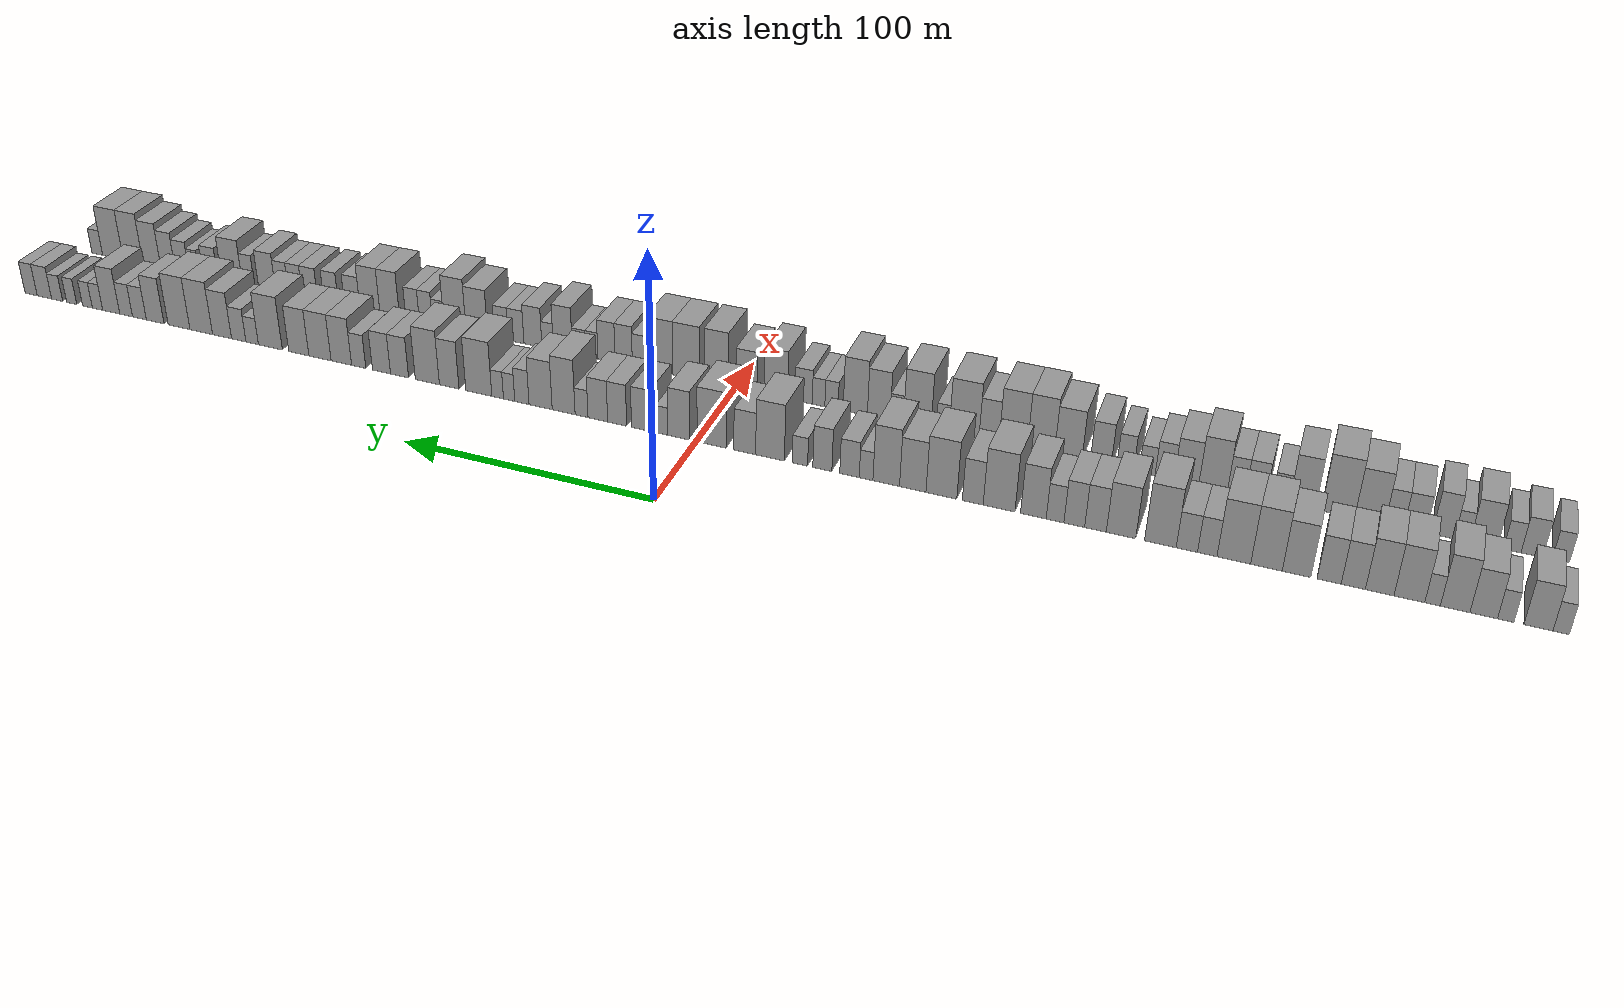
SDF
<sdf version="1.6">
 <world name="default">
  <scene>
   <sky><clouds><speed>12</speed></clouds></sky>
   <ambient>0.4 0.4 0.4 1</ambient>
   <background>0.7 0.7 0.7 1</background>
   <shadows>1</shadows>
  </scene>
  <gravity>0 0 -9.8066</gravity>
  <magnetic_field>6e-06 2.3e-05 -4.2e-05</magnetic_field>
  <physics default="0" name="default_physics" type="ode">
   <ode>
    <solver>
     <type>quick</type>
     <iters>10</iters>
     <sor>1.0</sor>
     <use_dynamic_moi_rescaling>0</use_dynamic_moi_rescaling>
    </solver>
    <constraints>
     <cfm>0</cfm>
     <erp>0.2</erp>
     <contact_max_correcting_vel>100</contact_max_correcting_vel>
     <contact_surface_layer>0.001</contact_surface_layer>
    </constraints>
   </ode>
   <max_step_size>0.004</max_step_size>
   <real_time_factor>1</real_time_factor>
   <real_time_update_rate>250</real_time_update_rate>
  </physics>
  <light name="sun" type="directional">
   <pose>0 0 10 0 0 0</pose>
   <diffuse>0.8 0.8 0.8 1</diffuse>
   <specular>0.2 0.2 0.2 1</specular>
   <attenuation>
    <range>1000</range>
    <constant>0.9</constant>
    <linear>0.01</linear>
    <quadratic>0.001</quadratic>
   </attenuation>
   <direction>-0.5 0.1 -0.9</direction>
  </light>
  <model name="building_1">
   <static>1</static>
   <pose>50.0000 -297.5715 0 0.000000 0.000000 0.000000</pose>
   <link name="link">
    <pose>0 0 6.00 0 0 0</pose>
    <collision name="collision"><geometry><box><size>20.0000 4.8570 12.0000</size></box></geometry></collision>
    <visual name="visual">
     <cast_shadows>0</cast_shadows>
     <geometry><box><size>20.0000 4.8570 12.0000</size></box></geometry>
     <material>
      <script>
       <uri>model://grey_wall/materials/scripts</uri>
       <uri>model://grey_wall/materials/textures</uri>
       <name>vrc/grey_wall</name>
      </script>
     </material>
    </visual>
   </link>
  </model>
  <model name="building_2">
   <static>1</static>
   <pose>50.0000 -290.7994 0 0.000000 0.000000 0.000000</pose>
   <link name="link">
    <pose>0 0 9.00 0 0 0</pose>
    <collision name="collision"><geometry><box><size>20.0000 8.6872 18.0000</size></box></geometry></collision>
    <visual name="visual">
     <cast_shadows>0</cast_shadows>
     <geometry><box><size>20.0000 8.6872 18.0000</size></box></geometry>
     <material>
      <script>
       <uri>model://grey_wall/materials/scripts</uri>
       <uri>model://grey_wall/materials/textures</uri>
       <name>vrc/grey_wall</name>
      </script>
     </material>
    </visual>
   </link>
  </model>
  <model name="building_3">
   <static>1</static>
   <pose>50.0000 -280.9802 0 0.000000 0.000000 0.000000</pose>
   <link name="link">
    <pose>0 0 6.00 0 0 0</pose>
    <collision name="collision"><geometry><box><size>20.0000 4.9514 12.0000</size></box></geometry></collision>
    <visual name="visual">
     <cast_shadows>0</cast_shadows>
     <geometry><box><size>20.0000 4.9514 12.0000</size></box></geometry>
     <material>
      <script>
       <uri>model://grey_wall/materials/scripts</uri>
       <uri>model://grey_wall/materials/textures</uri>
       <name>vrc/grey_wall</name>
      </script>
     </material>
    </visual>
   </link>
  </model>
  <model name="building_4">
   <static>1</static>
   <pose>50.0000 -274.3003 0 0.000000 0.000000 0.000000</pose>
   <link name="link">
    <pose>0 0 9.00 0 0 0</pose>
    <collision name="collision"><geometry><box><size>20.0000 8.4084 18.0000</size></box></geometry></collision>
    <visual name="visual">
     <cast_shadows>0</cast_shadows>
     <geometry><box><size>20.0000 8.4084 18.0000</size></box></geometry>
     <material>
      <script>
       <uri>model://grey_wall/materials/scripts</uri>
       <uri>model://grey_wall/materials/textures</uri>
       <name>vrc/grey_wall</name>
      </script>
     </material>
    </visual>
   </link>
  </model>
  <model name="building_5">
   <static>1</static>
   <pose>50.0000 -265.5569 0 0.000000 0.000000 0.000000</pose>
   <link name="link">
    <pose>0 0 10.50 0 0 0</pose>
    <collision name="collision"><geometry><box><size>20.0000 9.0783 21.0000</size></box></geometry></collision>
    <visual name="visual">
     <cast_shadows>0</cast_shadows>
     <geometry><box><size>20.0000 9.0783 21.0000</size></box></geometry>
     <material>
      <script>
       <uri>model://grey_wall/materials/scripts</uri>
       <uri>model://grey_wall/materials/textures</uri>
       <name>vrc/grey_wall</name>
      </script>
     </material>
    </visual>
   </link>
  </model>
  <model name="building_6">
   <static>1</static>
   <pose>50.0000 -258.6084 0 0.000000 0.000000 0.000000</pose>
   <link name="link">
    <pose>0 0 6.00 0 0 0</pose>
    <collision name="collision"><geometry><box><size>20.0000 4.8188 12.0000</size></box></geometry></collision>
    <visual name="visual">
     <cast_shadows>0</cast_shadows>
     <geometry><box><size>20.0000 4.8188 12.0000</size></box></geometry>
     <material>
      <script>
       <uri>model://grey_wall/materials/scripts</uri>
       <uri>model://grey_wall/materials/textures</uri>
       <name>vrc/grey_wall</name>
      </script>
     </material>
    </visual>
   </link>
  </model>
  <model name="building_7">
   <static>1</static>
   <pose>50.0000 -251.3825 0 0.000000 0.000000 0.000000</pose>
   <link name="link">
    <pose>0 0 10.50 0 0 0</pose>
    <collision name="collision"><geometry><box><size>20.0000 9.6330 21.0000</size></box></geometry></collision>
    <visual name="visual">
     <cast_shadows>0</cast_shadows>
     <geometry><box><size>20.0000 9.6330 21.0000</size></box></geometry>
     <material>
      <script>
       <uri>model://grey_wall/materials/scripts</uri>
       <uri>model://grey_wall/materials/textures</uri>
       <name>vrc/grey_wall</name>
      </script>
     </material>
    </visual>
   </link>
  </model>
  <model name="building_8">
   <static>1</static>
   <pose>50.0000 -242.0816 0 0.000000 0.000000 0.000000</pose>
   <link name="link">
    <pose>0 0 10.50 0 0 0</pose>
    <collision name="collision"><geometry><box><size>20.0000 8.9687 21.0000</size></box></geometry></collision>
    <visual name="visual">
     <cast_shadows>0</cast_shadows>
     <geometry><box><size>20.0000 8.9687 21.0000</size></box></geometry>
     <material>
      <script>
       <uri>model://grey_wall/materials/scripts</uri>
       <uri>model://grey_wall/materials/textures</uri>
       <name>vrc/grey_wall</name>
      </script>
     </material>
    </visual>
   </link>
  </model>
  <model name="building_9">
   <static>1</static>
   <pose>50.0000 -233.7496 0 0.000000 0.000000 0.000000</pose>
   <link name="link">
    <pose>0 0 9.00 0 0 0</pose>
    <collision name="collision"><geometry><box><size>20.0000 7.6954 18.0000</size></box></geometry></collision>
    <visual name="visual">
     <cast_shadows>0</cast_shadows>
     <geometry><box><size>20.0000 7.6954 18.0000</size></box></geometry>
     <material>
      <script>
       <uri>model://grey_wall/materials/scripts</uri>
       <uri>model://grey_wall/materials/textures</uri>
       <name>vrc/grey_wall</name>
      </script>
     </material>
    </visual>
   </link>
  </model>
  <model name="building_10">
   <static>1</static>
   <pose>50.0000 -226.0455 0 0.000000 0.000000 0.000000</pose>
   <link name="link">
    <pose>0 0 9.00 0 0 0</pose>
    <collision name="collision"><geometry><box><size>20.0000 7.7126 18.0000</size></box></geometry></collision>
    <visual name="visual">
     <cast_shadows>0</cast_shadows>
     <geometry><box><size>20.0000 7.7126 18.0000</size></box></geometry>
     <material>
      <script>
       <uri>model://grey_wall/materials/scripts</uri>
       <uri>model://grey_wall/materials/textures</uri>
       <name>vrc/grey_wall</name>
      </script>
     </material>
    </visual>
   </link>
  </model>
  <model name="building_11">
   <static>1</static>
   <pose>50.0000 -215.5581 0 0.000000 0.000000 0.000000</pose>
   <link name="link">
    <pose>0 0 10.50 0 0 0</pose>
    <collision name="collision"><geometry><box><size>20.0000 9.2623 21.0000</size></box></geometry></collision>
    <visual name="visual">
     <cast_shadows>0</cast_shadows>
     <geometry><box><size>20.0000 9.2623 21.0000</size></box></geometry>
     <material>
      <script>
       <uri>model://grey_wall/materials/scripts</uri>
       <uri>model://grey_wall/materials/textures</uri>
       <name>vrc/grey_wall</name>
      </script>
     </material>
    </visual>
   </link>
  </model>
  <model name="building_12">
   <static>1</static>
   <pose>50.0000 -205.7762 0 0.000000 0.000000 0.000000</pose>
   <link name="link">
    <pose>0 0 12.00 0 0 0</pose>
    <collision name="collision"><geometry><box><size>20.0000 10.3015 24.0000</size></box></geometry></collision>
    <visual name="visual">
     <cast_shadows>0</cast_shadows>
     <geometry><box><size>20.0000 10.3015 24.0000</size></box></geometry>
     <material>
      <script>
       <uri>model://grey_wall/materials/scripts</uri>
       <uri>model://grey_wall/materials/textures</uri>
       <name>vrc/grey_wall</name>
      </script>
     </material>
    </visual>
   </link>
  </model>
  <model name="building_13">
   <static>1</static>
   <pose>50.0000 -195.0669 0 0.000000 0.000000 0.000000</pose>
   <link name="link">
    <pose>0 0 12.00 0 0 0</pose>
    <collision name="collision"><geometry><box><size>20.0000 11.1171 24.0000</size></box></geometry></collision>
    <visual name="visual">
     <cast_shadows>0</cast_shadows>
     <geometry><box><size>20.0000 11.1171 24.0000</size></box></geometry>
     <material>
      <script>
       <uri>model://grey_wall/materials/scripts</uri>
       <uri>model://grey_wall/materials/textures</uri>
       <name>vrc/grey_wall</name>
      </script>
     </material>
    </visual>
   </link>
  </model>
  <model name="building_14">
   <static>1</static>
   <pose>50.0000 -186.2584 0 0.000000 0.000000 0.000000</pose>
   <link name="link">
    <pose>0 0 7.50 0 0 0</pose>
    <collision name="collision"><geometry><box><size>20.0000 6.4999 15.0000</size></box></geometry></collision>
    <visual name="visual">
     <cast_shadows>0</cast_shadows>
     <geometry><box><size>20.0000 6.4999 15.0000</size></box></geometry>
     <material>
      <script>
       <uri>model://grey_wall/materials/scripts</uri>
       <uri>model://grey_wall/materials/textures</uri>
       <name>vrc/grey_wall</name>
      </script>
     </material>
    </visual>
   </link>
  </model>
  <model name="building_15">
   <static>1</static>
   <pose>50.0000 -179.4305 0 0.000000 0.000000 0.000000</pose>
   <link name="link">
    <pose>0 0 7.50 0 0 0</pose>
    <collision name="collision"><geometry><box><size>20.0000 7.1558 15.0000</size></box></geometry></collision>
    <visual name="visual">
     <cast_shadows>0</cast_shadows>
     <geometry><box><size>20.0000 7.1558 15.0000</size></box></geometry>
     <material>
      <script>
       <uri>model://grey_wall/materials/scripts</uri>
       <uri>model://grey_wall/materials/textures</uri>
       <name>vrc/grey_wall</name>
      </script>
     </material>
    </visual>
   </link>
  </model>
  <model name="building_16">
   <static>1</static>
   <pose>50.0000 -170.4923 0 0.000000 0.000000 0.000000</pose>
   <link name="link">
    <pose>0 0 12.00 0 0 0</pose>
    <collision name="collision"><geometry><box><size>20.0000 10.7208 24.0000</size></box></geometry></collision>
    <visual name="visual">
     <cast_shadows>0</cast_shadows>
     <geometry><box><size>20.0000 10.7208 24.0000</size></box></geometry>
     <material>
      <script>
       <uri>model://grey_wall/materials/scripts</uri>
       <uri>model://grey_wall/materials/textures</uri>
       <name>vrc/grey_wall</name>
      </script>
     </material>
    </visual>
   </link>
  </model>
  <model name="building_17">
   <static>1</static>
   <pose>50.0000 -157.0809 0 0.000000 0.000000 0.000000</pose>
   <link name="link">
    <pose>0 0 10.50 0 0 0</pose>
    <collision name="collision"><geometry><box><size>20.0000 10.1021 21.0000</size></box></geometry></collision>
    <visual name="visual">
     <cast_shadows>0</cast_shadows>
     <geometry><box><size>20.0000 10.1021 21.0000</size></box></geometry>
     <material>
      <script>
       <uri>model://grey_wall/materials/scripts</uri>
       <uri>model://grey_wall/materials/textures</uri>
       <name>vrc/grey_wall</name>
      </script>
     </material>
    </visual>
   </link>
  </model>
  <model name="building_18">
   <static>1</static>
   <pose>50.0000 -148.2817 0 0.000000 0.000000 0.000000</pose>
   <link name="link">
    <pose>0 0 9.00 0 0 0</pose>
    <collision name="collision"><geometry><box><size>20.0000 7.4962 18.0000</size></box></geometry></collision>
    <visual name="visual">
     <cast_shadows>0</cast_shadows>
     <geometry><box><size>20.0000 7.4962 18.0000</size></box></geometry>
     <material>
      <script>
       <uri>model://grey_wall/materials/scripts</uri>
       <uri>model://grey_wall/materials/textures</uri>
       <name>vrc/grey_wall</name>
      </script>
     </material>
    </visual>
   </link>
  </model>
  <model name="building_19">
   <static>1</static>
   <pose>50.0000 -140.9135 0 0.000000 0.000000 0.000000</pose>
   <link name="link">
    <pose>0 0 9.00 0 0 0</pose>
    <collision name="collision"><geometry><box><size>20.0000 7.2403 18.0000</size></box></geometry></collision>
    <visual name="visual">
     <cast_shadows>0</cast_shadows>
     <geometry><box><size>20.0000 7.2403 18.0000</size></box></geometry>
     <material>
      <script>
       <uri>model://grey_wall/materials/scripts</uri>
       <uri>model://grey_wall/materials/textures</uri>
       <name>vrc/grey_wall</name>
      </script>
     </material>
    </visual>
   </link>
  </model>
  <model name="building_20">
   <static>1</static>
   <pose>50.0000 -134.1900 0 0.000000 0.000000 0.000000</pose>
   <link name="link">
    <pose>0 0 7.50 0 0 0</pose>
    <collision name="collision"><geometry><box><size>20.0000 6.2068 15.0000</size></box></geometry></collision>
    <visual name="visual">
     <cast_shadows>0</cast_shadows>
     <geometry><box><size>20.0000 6.2068 15.0000</size></box></geometry>
     <material>
      <script>
       <uri>model://grey_wall/materials/scripts</uri>
       <uri>model://grey_wall/materials/textures</uri>
       <name>vrc/grey_wall</name>
      </script>
     </material>
    </visual>
   </link>
  </model>
  <model name="building_21">
   <static>1</static>
   <pose>50.0000 -126.5503 0 0.000000 0.000000 0.000000</pose>
   <link name="link">
    <pose>0 0 10.50 0 0 0</pose>
    <collision name="collision"><geometry><box><size>20.0000 9.0725 21.0000</size></box></geometry></collision>
    <visual name="visual">
     <cast_shadows>0</cast_shadows>
     <geometry><box><size>20.0000 9.0725 21.0000</size></box></geometry>
     <material>
      <script>
       <uri>model://grey_wall/materials/scripts</uri>
       <uri>model://grey_wall/materials/textures</uri>
       <name>vrc/grey_wall</name>
      </script>
     </material>
    </visual>
   </link>
  </model>
  <model name="building_22">
   <static>1</static>
   <pose>50.0000 -114.3188 0 0.000000 0.000000 0.000000</pose>
   <link name="link">
    <pose>0 0 12.00 0 0 0</pose>
    <collision name="collision"><geometry><box><size>20.0000 11.3905 24.0000</size></box></geometry></collision>
    <visual name="visual">
     <cast_shadows>0</cast_shadows>
     <geometry><box><size>20.0000 11.3905 24.0000</size></box></geometry>
     <material>
      <script>
       <uri>model://grey_wall/materials/scripts</uri>
       <uri>model://grey_wall/materials/textures</uri>
       <name>vrc/grey_wall</name>
      </script>
     </material>
    </visual>
   </link>
  </model>
  <model name="building_23">
   <static>1</static>
   <pose>50.0000 -104.8672 0 0.000000 0.000000 0.000000</pose>
   <link name="link">
    <pose>0 0 9.00 0 0 0</pose>
    <collision name="collision"><geometry><box><size>20.0000 7.5128 18.0000</size></box></geometry></collision>
    <visual name="visual">
     <cast_shadows>0</cast_shadows>
     <geometry><box><size>20.0000 7.5128 18.0000</size></box></geometry>
     <material>
      <script>
       <uri>model://grey_wall/materials/scripts</uri>
       <uri>model://grey_wall/materials/textures</uri>
       <name>vrc/grey_wall</name>
      </script>
     </material>
    </visual>
   </link>
  </model>
  <model name="building_24">
   <static>1</static>
   <pose>50.0000 -93.4741 0 0.000000 0.000000 0.000000</pose>
   <link name="link">
    <pose>0 0 12.00 0 0 0</pose>
    <collision name="collision"><geometry><box><size>20.0000 11.2733 24.0000</size></box></geometry></collision>
    <visual name="visual">
     <cast_shadows>0</cast_shadows>
     <geometry><box><size>20.0000 11.2733 24.0000</size></box></geometry>
     <material>
      <script>
       <uri>model://grey_wall/materials/scripts</uri>
       <uri>model://grey_wall/materials/textures</uri>
       <name>vrc/grey_wall</name>
      </script>
     </material>
    </visual>
   </link>
  </model>
  <model name="building_25">
   <static>1</static>
   <pose>50.0000 -82.9544 0 0.000000 0.000000 0.000000</pose>
   <link name="link">
    <pose>0 0 10.50 0 0 0</pose>
    <collision name="collision"><geometry><box><size>20.0000 9.7661 21.0000</size></box></geometry></collision>
    <visual name="visual">
     <cast_shadows>0</cast_shadows>
     <geometry><box><size>20.0000 9.7661 21.0000</size></box></geometry>
     <material>
      <script>
       <uri>model://grey_wall/materials/scripts</uri>
       <uri>model://grey_wall/materials/textures</uri>
       <name>vrc/grey_wall</name>
      </script>
     </material>
    </visual>
   </link>
  </model>
  <model name="building_26">
   <static>1</static>
   <pose>50.0000 -73.1143 0 0.000000 0.000000 0.000000</pose>
   <link name="link">
    <pose>0 0 12.00 0 0 0</pose>
    <collision name="collision"><geometry><box><size>20.0000 9.9142 24.0000</size></box></geometry></collision>
    <visual name="visual">
     <cast_shadows>0</cast_shadows>
     <geometry><box><size>20.0000 9.9142 24.0000</size></box></geometry>
     <material>
      <script>
       <uri>model://grey_wall/materials/scripts</uri>
       <uri>model://grey_wall/materials/textures</uri>
       <name>vrc/grey_wall</name>
      </script>
     </material>
    </visual>
   </link>
  </model>
  <model name="building_27">
   <static>1</static>
   <pose>50.0000 -65.5913 0 0.000000 0.000000 0.000000</pose>
   <link name="link">
    <pose>0 0 6.00 0 0 0</pose>
    <collision name="collision"><geometry><box><size>20.0000 5.1318 12.0000</size></box></geometry></collision>
    <visual name="visual">
     <cast_shadows>0</cast_shadows>
     <geometry><box><size>20.0000 5.1318 12.0000</size></box></geometry>
     <material>
      <script>
       <uri>model://grey_wall/materials/scripts</uri>
       <uri>model://grey_wall/materials/textures</uri>
       <name>vrc/grey_wall</name>
      </script>
     </material>
    </visual>
   </link>
  </model>
  <model name="building_28">
   <static>1</static>
   <pose>50.0000 -59.3571 0 0.000000 0.000000 0.000000</pose>
   <link name="link">
    <pose>0 0 7.50 0 0 0</pose>
    <collision name="collision"><geometry><box><size>20.0000 7.3364 15.0000</size></box></geometry></collision>
    <visual name="visual">
     <cast_shadows>0</cast_shadows>
     <geometry><box><size>20.0000 7.3364 15.0000</size></box></geometry>
     <material>
      <script>
       <uri>model://grey_wall/materials/scripts</uri>
       <uri>model://grey_wall/materials/textures</uri>
       <name>vrc/grey_wall</name>
      </script>
     </material>
    </visual>
   </link>
  </model>
  <model name="building_29">
   <static>1</static>
   <pose>50.0000 -49.0608 0 0.000000 0.000000 0.000000</pose>
   <link name="link">
    <pose>0 0 9.00 0 0 0</pose>
    <collision name="collision"><geometry><box><size>20.0000 7.2563 18.0000</size></box></geometry></collision>
    <visual name="visual">
     <cast_shadows>0</cast_shadows>
     <geometry><box><size>20.0000 7.2563 18.0000</size></box></geometry>
     <material>
      <script>
       <uri>model://grey_wall/materials/scripts</uri>
       <uri>model://grey_wall/materials/textures</uri>
       <name>vrc/grey_wall</name>
      </script>
     </material>
    </visual>
   </link>
  </model>
  <model name="building_30">
   <static>1</static>
   <pose>50.0000 -40.4750 0 0.000000 0.000000 0.000000</pose>
   <link name="link">
    <pose>0 0 6.00 0 0 0</pose>
    <collision name="collision"><geometry><box><size>20.0000 5.9151 12.0000</size></box></geometry></collision>
    <visual name="visual">
     <cast_shadows>0</cast_shadows>
     <geometry><box><size>20.0000 5.9151 12.0000</size></box></geometry>
     <material>
      <script>
       <uri>model://grey_wall/materials/scripts</uri>
       <uri>model://grey_wall/materials/textures</uri>
       <name>vrc/grey_wall</name>
      </script>
     </material>
    </visual>
   </link>
  </model>
  <model name="building_31">
   <static>1</static>
   <pose>50.0000 -28.9358 0 0.000000 0.000000 0.000000</pose>
   <link name="link">
    <pose>0 0 12.00 0 0 0</pose>
    <collision name="collision"><geometry><box><size>20.0000 11.1633 24.0000</size></box></geometry></collision>
    <visual name="visual">
     <cast_shadows>0</cast_shadows>
     <geometry><box><size>20.0000 11.1633 24.0000</size></box></geometry>
     <material>
      <script>
       <uri>model://grey_wall/materials/scripts</uri>
       <uri>model://grey_wall/materials/textures</uri>
       <name>vrc/grey_wall</name>
      </script>
     </material>
    </visual>
   </link>
  </model>
  <model name="building_32">
   <static>1</static>
   <pose>50.0000 -19.0690 0 0.000000 0.000000 0.000000</pose>
   <link name="link">
    <pose>0 0 9.00 0 0 0</pose>
    <collision name="collision"><geometry><box><size>20.0000 8.5704 18.0000</size></box></geometry></collision>
    <visual name="visual">
     <cast_shadows>0</cast_shadows>
     <geometry><box><size>20.0000 8.5704 18.0000</size></box></geometry>
     <material>
      <script>
       <uri>model://grey_wall/materials/scripts</uri>
       <uri>model://grey_wall/materials/textures</uri>
       <name>vrc/grey_wall</name>
      </script>
     </material>
    </visual>
   </link>
  </model>
  <model name="building_33">
   <static>1</static>
   <pose>50.0000 -6.0298 0 0.000000 0.000000 0.000000</pose>
   <link name="link">
    <pose>0 0 12.00 0 0 0</pose>
    <collision name="collision"><geometry><box><size>20.0000 11.5079 24.0000</size></box></geometry></collision>
    <visual name="visual">
     <cast_shadows>0</cast_shadows>
     <geometry><box><size>20.0000 11.5079 24.0000</size></box></geometry>
     <material>
      <script>
       <uri>model://grey_wall/materials/scripts</uri>
       <uri>model://grey_wall/materials/textures</uri>
       <name>vrc/grey_wall</name>
      </script>
     </material>
    </visual>
   </link>
  </model>
  <model name="building_34">
   <static>1</static>
   <pose>50.0000 7.1088 0 0.000000 0.000000 0.000000</pose>
   <link name="link">
    <pose>0 0 10.50 0 0 0</pose>
    <collision name="collision"><geometry><box><size>20.0000 8.7692 21.0000</size></box></geometry></collision>
    <visual name="visual">
     <cast_shadows>0</cast_shadows>
     <geometry><box><size>20.0000 8.7692 21.0000</size></box></geometry>
     <material>
      <script>
       <uri>model://grey_wall/materials/scripts</uri>
       <uri>model://grey_wall/materials/textures</uri>
       <name>vrc/grey_wall</name>
      </script>
     </material>
    </visual>
   </link>
  </model>
  <model name="building_35">
   <static>1</static>
   <pose>50.0000 13.9240 0 0.000000 0.000000 0.000000</pose>
   <link name="link">
    <pose>0 0 6.00 0 0 0</pose>
    <collision name="collision"><geometry><box><size>20.0000 4.8613 12.0000</size></box></geometry></collision>
    <visual name="visual">
     <cast_shadows>0</cast_shadows>
     <geometry><box><size>20.0000 4.8613 12.0000</size></box></geometry>
     <material>
      <script>
       <uri>model://grey_wall/materials/scripts</uri>
       <uri>model://grey_wall/materials/textures</uri>
       <name>vrc/grey_wall</name>
      </script>
     </material>
    </visual>
   </link>
  </model>
  <model name="building_36">
   <static>1</static>
   <pose>50.0000 22.3026 0 0.000000 0.000000 0.000000</pose>
   <link name="link">
    <pose>0 0 9.00 0 0 0</pose>
    <collision name="collision"><geometry><box><size>20.0000 7.8958 18.0000</size></box></geometry></collision>
    <visual name="visual">
     <cast_shadows>0</cast_shadows>
     <geometry><box><size>20.0000 7.8958 18.0000</size></box></geometry>
     <material>
      <script>
       <uri>model://grey_wall/materials/scripts</uri>
       <uri>model://grey_wall/materials/textures</uri>
       <name>vrc/grey_wall</name>
      </script>
     </material>
    </visual>
   </link>
  </model>
  <model name="building_37">
   <static>1</static>
   <pose>50.0000 32.1609 0 0.000000 0.000000 0.000000</pose>
   <link name="link">
    <pose>0 0 9.00 0 0 0</pose>
    <collision name="collision"><geometry><box><size>20.0000 7.8208 18.0000</size></box></geometry></collision>
    <visual name="visual">
     <cast_shadows>0</cast_shadows>
     <geometry><box><size>20.0000 7.8208 18.0000</size></box></geometry>
     <material>
      <script>
       <uri>model://grey_wall/materials/scripts</uri>
       <uri>model://grey_wall/materials/textures</uri>
       <name>vrc/grey_wall</name>
      </script>
     </material>
    </visual>
   </link>
  </model>
  <model name="building_38">
   <static>1</static>
   <pose>50.0000 40.1350 0 0.000000 0.000000 0.000000</pose>
   <link name="link">
    <pose>0 0 9.00 0 0 0</pose>
    <collision name="collision"><geometry><box><size>20.0000 8.1274 18.0000</size></box></geometry></collision>
    <visual name="visual">
     <cast_shadows>0</cast_shadows>
     <geometry><box><size>20.0000 8.1274 18.0000</size></box></geometry>
     <material>
      <script>
       <uri>model://grey_wall/materials/scripts</uri>
       <uri>model://grey_wall/materials/textures</uri>
       <name>vrc/grey_wall</name>
      </script>
     </material>
    </visual>
   </link>
  </model>
  <model name="building_39">
   <static>1</static>
   <pose>50.0000 46.8901 0 0.000000 0.000000 0.000000</pose>
   <link name="link">
    <pose>0 0 6.00 0 0 0</pose>
    <collision name="collision"><geometry><box><size>20.0000 5.3828 12.0000</size></box></geometry></collision>
    <visual name="visual">
     <cast_shadows>0</cast_shadows>
     <geometry><box><size>20.0000 5.3828 12.0000</size></box></geometry>
     <material>
      <script>
       <uri>model://grey_wall/materials/scripts</uri>
       <uri>model://grey_wall/materials/textures</uri>
       <name>vrc/grey_wall</name>
      </script>
     </material>
    </visual>
   </link>
  </model>
  <model name="building_40">
   <static>1</static>
   <pose>50.0000 54.3845 0 0.000000 0.000000 0.000000</pose>
   <link name="link">
    <pose>0 0 12.00 0 0 0</pose>
    <collision name="collision"><geometry><box><size>20.0000 9.6059 24.0000</size></box></geometry></collision>
    <visual name="visual">
     <cast_shadows>0</cast_shadows>
     <geometry><box><size>20.0000 9.6059 24.0000</size></box></geometry>
     <material>
      <script>
       <uri>model://grey_wall/materials/scripts</uri>
       <uri>model://grey_wall/materials/textures</uri>
       <name>vrc/grey_wall</name>
      </script>
     </material>
    </visual>
   </link>
  </model>
  <model name="building_41">
   <static>1</static>
   <pose>50.0000 64.0913 0 0.000000 0.000000 0.000000</pose>
   <link name="link">
    <pose>0 0 10.50 0 0 0</pose>
    <collision name="collision"><geometry><box><size>20.0000 9.8076 21.0000</size></box></geometry></collision>
    <visual name="visual">
     <cast_shadows>0</cast_shadows>
     <geometry><box><size>20.0000 9.8076 21.0000</size></box></geometry>
     <material>
      <script>
       <uri>model://grey_wall/materials/scripts</uri>
       <uri>model://grey_wall/materials/textures</uri>
       <name>vrc/grey_wall</name>
      </script>
     </material>
    </visual>
   </link>
  </model>
  <model name="building_42">
   <static>1</static>
   <pose>50.0000 72.0387 0 0.000000 0.000000 0.000000</pose>
   <link name="link">
    <pose>0 0 7.50 0 0 0</pose>
    <collision name="collision"><geometry><box><size>20.0000 6.0873 15.0000</size></box></geometry></collision>
    <visual name="visual">
     <cast_shadows>0</cast_shadows>
     <geometry><box><size>20.0000 6.0873 15.0000</size></box></geometry>
     <material>
      <script>
       <uri>model://grey_wall/materials/scripts</uri>
       <uri>model://grey_wall/materials/textures</uri>
       <name>vrc/grey_wall</name>
      </script>
     </material>
    </visual>
   </link>
  </model>
  <model name="building_43">
   <static>1</static>
   <pose>50.0000 77.4882 0 0.000000 0.000000 0.000000</pose>
   <link name="link">
    <pose>0 0 6.00 0 0 0</pose>
    <collision name="collision"><geometry><box><size>20.0000 4.8118 12.0000</size></box></geometry></collision>
    <visual name="visual">
     <cast_shadows>0</cast_shadows>
     <geometry><box><size>20.0000 4.8118 12.0000</size></box></geometry>
     <material>
      <script>
       <uri>model://grey_wall/materials/scripts</uri>
       <uri>model://grey_wall/materials/textures</uri>
       <name>vrc/grey_wall</name>
      </script>
     </material>
    </visual>
   </link>
  </model>
  <model name="building_44">
   <static>1</static>
   <pose>50.0000 82.4046 0 0.000000 0.000000 0.000000</pose>
   <link name="link">
    <pose>0 0 6.00 0 0 0</pose>
    <collision name="collision"><geometry><box><size>20.0000 5.0209 12.0000</size></box></geometry></collision>
    <visual name="visual">
     <cast_shadows>0</cast_shadows>
     <geometry><box><size>20.0000 5.0209 12.0000</size></box></geometry>
     <material>
      <script>
       <uri>model://grey_wall/materials/scripts</uri>
       <uri>model://grey_wall/materials/textures</uri>
       <name>vrc/grey_wall</name>
      </script>
     </material>
    </visual>
   </link>
  </model>
  <model name="building_45">
   <static>1</static>
   <pose>50.0000 90.5324 0 0.000000 0.000000 0.000000</pose>
   <link name="link">
    <pose>0 0 12.00 0 0 0</pose>
    <collision name="collision"><geometry><box><size>20.0000 11.2347 24.0000</size></box></geometry></collision>
    <visual name="visual">
     <cast_shadows>0</cast_shadows>
     <geometry><box><size>20.0000 11.2347 24.0000</size></box></geometry>
     <material>
      <script>
       <uri>model://grey_wall/materials/scripts</uri>
       <uri>model://grey_wall/materials/textures</uri>
       <name>vrc/grey_wall</name>
      </script>
     </material>
    </visual>
   </link>
  </model>
  <model name="building_46">
   <static>1</static>
   <pose>50.0000 103.4537 0 0.000000 0.000000 0.000000</pose>
   <link name="link">
    <pose>0 0 10.50 0 0 0</pose>
    <collision name="collision"><geometry><box><size>20.0000 8.6078 21.0000</size></box></geometry></collision>
    <visual name="visual">
     <cast_shadows>0</cast_shadows>
     <geometry><box><size>20.0000 8.6078 21.0000</size></box></geometry>
     <material>
      <script>
       <uri>model://grey_wall/materials/scripts</uri>
       <uri>model://grey_wall/materials/textures</uri>
       <name>vrc/grey_wall</name>
      </script>
     </material>
    </visual>
   </link>
  </model>
  <model name="building_47">
   <static>1</static>
   <pose>50.0000 113.0710 0 0.000000 0.000000 0.000000</pose>
   <link name="link">
    <pose>0 0 12.00 0 0 0</pose>
    <collision name="collision"><geometry><box><size>20.0000 10.6269 24.0000</size></box></geometry></collision>
    <visual name="visual">
     <cast_shadows>0</cast_shadows>
     <geometry><box><size>20.0000 10.6269 24.0000</size></box></geometry>
     <material>
      <script>
       <uri>model://grey_wall/materials/scripts</uri>
       <uri>model://grey_wall/materials/textures</uri>
       <name>vrc/grey_wall</name>
      </script>
     </material>
    </visual>
   </link>
  </model>
  <model name="building_48">
   <static>1</static>
   <pose>50.0000 125.4324 0 0.000000 0.000000 0.000000</pose>
   <link name="link">
    <pose>0 0 9.00 0 0 0</pose>
    <collision name="collision"><geometry><box><size>20.0000 8.0960 18.0000</size></box></geometry></collision>
    <visual name="visual">
     <cast_shadows>0</cast_shadows>
     <geometry><box><size>20.0000 8.0960 18.0000</size></box></geometry>
     <material>
      <script>
       <uri>model://grey_wall/materials/scripts</uri>
       <uri>model://grey_wall/materials/textures</uri>
       <name>vrc/grey_wall</name>
      </script>
     </material>
    </visual>
   </link>
  </model>
  <model name="building_49">
   <static>1</static>
   <pose>50.0000 133.5288 0 0.000000 0.000000 0.000000</pose>
   <link name="link">
    <pose>0 0 9.00 0 0 0</pose>
    <collision name="collision"><geometry><box><size>20.0000 8.0967 18.0000</size></box></geometry></collision>
    <visual name="visual">
     <cast_shadows>0</cast_shadows>
     <geometry><box><size>20.0000 8.0967 18.0000</size></box></geometry>
     <material>
      <script>
       <uri>model://grey_wall/materials/scripts</uri>
       <uri>model://grey_wall/materials/textures</uri>
       <name>vrc/grey_wall</name>
      </script>
     </material>
    </visual>
   </link>
  </model>
  <model name="building_50">
   <static>1</static>
   <pose>50.0000 143.8036 0 0.000000 0.000000 0.000000</pose>
   <link name="link">
    <pose>0 0 7.50 0 0 0</pose>
    <collision name="collision"><geometry><box><size>20.0000 6.4529 15.0000</size></box></geometry></collision>
    <visual name="visual">
     <cast_shadows>0</cast_shadows>
     <geometry><box><size>20.0000 6.4529 15.0000</size></box></geometry>
     <material>
      <script>
       <uri>model://grey_wall/materials/scripts</uri>
       <uri>model://grey_wall/materials/textures</uri>
       <name>vrc/grey_wall</name>
      </script>
     </material>
    </visual>
   </link>
  </model>
  <model name="building_51">
   <static>1</static>
   <pose>50.0000 151.7196 0 0.000000 0.000000 0.000000</pose>
   <link name="link">
    <pose>0 0 10.50 0 0 0</pose>
    <collision name="collision"><geometry><box><size>20.0000 9.3789 21.0000</size></box></geometry></collision>
    <visual name="visual">
     <cast_shadows>0</cast_shadows>
     <geometry><box><size>20.0000 9.3789 21.0000</size></box></geometry>
     <material>
      <script>
       <uri>model://grey_wall/materials/scripts</uri>
       <uri>model://grey_wall/materials/textures</uri>
       <name>vrc/grey_wall</name>
      </script>
     </material>
    </visual>
   </link>
  </model>
  <model name="building_52">
   <static>1</static>
   <pose>50.0000 161.5424 0 0.000000 0.000000 0.000000</pose>
   <link name="link">
    <pose>0 0 10.50 0 0 0</pose>
    <collision name="collision"><geometry><box><size>20.0000 10.2667 21.0000</size></box></geometry></collision>
    <visual name="visual">
     <cast_shadows>0</cast_shadows>
     <geometry><box><size>20.0000 10.2667 21.0000</size></box></geometry>
     <material>
      <script>
       <uri>model://grey_wall/materials/scripts</uri>
       <uri>model://grey_wall/materials/textures</uri>
       <name>vrc/grey_wall</name>
      </script>
     </material>
    </visual>
   </link>
  </model>
  <model name="building_53">
   <static>1</static>
   <pose>50.0000 171.3436 0 0.000000 0.000000 0.000000</pose>
   <link name="link">
    <pose>0 0 10.50 0 0 0</pose>
    <collision name="collision"><geometry><box><size>20.0000 9.3358 21.0000</size></box></geometry></collision>
    <visual name="visual">
     <cast_shadows>0</cast_shadows>
     <geometry><box><size>20.0000 9.3358 21.0000</size></box></geometry>
     <material>
      <script>
       <uri>model://grey_wall/materials/scripts</uri>
       <uri>model://grey_wall/materials/textures</uri>
       <name>vrc/grey_wall</name>
      </script>
     </material>
    </visual>
   </link>
  </model>
  <model name="building_54">
   <static>1</static>
   <pose>50.0000 184.6445 0 0.000000 0.000000 0.000000</pose>
   <link name="link">
    <pose>0 0 12.00 0 0 0</pose>
    <collision name="collision"><geometry><box><size>20.0000 11.2659 24.0000</size></box></geometry></collision>
    <visual name="visual">
     <cast_shadows>0</cast_shadows>
     <geometry><box><size>20.0000 11.2659 24.0000</size></box></geometry>
     <material>
      <script>
       <uri>model://grey_wall/materials/scripts</uri>
       <uri>model://grey_wall/materials/textures</uri>
       <name>vrc/grey_wall</name>
      </script>
     </material>
    </visual>
   </link>
  </model>
  <model name="building_55">
   <static>1</static>
   <pose>50.0000 193.2278 0 0.000000 0.000000 0.000000</pose>
   <link name="link">
    <pose>0 0 6.00 0 0 0</pose>
    <collision name="collision"><geometry><box><size>20.0000 5.9009 12.0000</size></box></geometry></collision>
    <visual name="visual">
     <cast_shadows>0</cast_shadows>
     <geometry><box><size>20.0000 5.9009 12.0000</size></box></geometry>
     <material>
      <script>
       <uri>model://grey_wall/materials/scripts</uri>
       <uri>model://grey_wall/materials/textures</uri>
       <name>vrc/grey_wall</name>
      </script>
     </material>
    </visual>
   </link>
  </model>
  <model name="building_56">
   <static>1</static>
   <pose>50.0000 199.6031 0 0.000000 0.000000 0.000000</pose>
   <link name="link">
    <pose>0 0 7.50 0 0 0</pose>
    <collision name="collision"><geometry><box><size>20.0000 6.8497 15.0000</size></box></geometry></collision>
    <visual name="visual">
     <cast_shadows>0</cast_shadows>
     <geometry><box><size>20.0000 6.8497 15.0000</size></box></geometry>
     <material>
      <script>
       <uri>model://grey_wall/materials/scripts</uri>
       <uri>model://grey_wall/materials/textures</uri>
       <name>vrc/grey_wall</name>
      </script>
     </material>
    </visual>
   </link>
  </model>
  <model name="building_57">
   <static>1</static>
   <pose>50.0000 207.5885 0 0.000000 0.000000 0.000000</pose>
   <link name="link">
    <pose>0 0 10.50 0 0 0</pose>
    <collision name="collision"><geometry><box><size>20.0000 9.1211 21.0000</size></box></geometry></collision>
    <visual name="visual">
     <cast_shadows>0</cast_shadows>
     <geometry><box><size>20.0000 9.1211 21.0000</size></box></geometry>
     <material>
      <script>
       <uri>model://grey_wall/materials/scripts</uri>
       <uri>model://grey_wall/materials/textures</uri>
       <name>vrc/grey_wall</name>
      </script>
     </material>
    </visual>
   </link>
  </model>
  <model name="building_58">
   <static>1</static>
   <pose>50.0000 217.6149 0 0.000000 0.000000 0.000000</pose>
   <link name="link">
    <pose>0 0 12.00 0 0 0</pose>
    <collision name="collision"><geometry><box><size>20.0000 10.9317 24.0000</size></box></geometry></collision>
    <visual name="visual">
     <cast_shadows>0</cast_shadows>
     <geometry><box><size>20.0000 10.9317 24.0000</size></box></geometry>
     <material>
      <script>
       <uri>model://grey_wall/materials/scripts</uri>
       <uri>model://grey_wall/materials/textures</uri>
       <name>vrc/grey_wall</name>
      </script>
     </material>
    </visual>
   </link>
  </model>
  <model name="building_59">
   <static>1</static>
   <pose>50.0000 228.4080 0 0.000000 0.000000 0.000000</pose>
   <link name="link">
    <pose>0 0 12.00 0 0 0</pose>
    <collision name="collision"><geometry><box><size>20.0000 10.6546 24.0000</size></box></geometry></collision>
    <visual name="visual">
     <cast_shadows>0</cast_shadows>
     <geometry><box><size>20.0000 10.6546 24.0000</size></box></geometry>
     <material>
      <script>
       <uri>model://grey_wall/materials/scripts</uri>
       <uri>model://grey_wall/materials/textures</uri>
       <name>vrc/grey_wall</name>
      </script>
     </material>
    </visual>
   </link>
  </model>
  <model name="building_60">
   <static>1</static>
   <pose>50.0000 240.0956 0 0.000000 0.000000 0.000000</pose>
   <link name="link">
    <pose>0 0 10.50 0 0 0</pose>
    <collision name="collision"><geometry><box><size>20.0000 8.7206 21.0000</size></box></geometry></collision>
    <visual name="visual">
     <cast_shadows>0</cast_shadows>
     <geometry><box><size>20.0000 8.7206 21.0000</size></box></geometry>
     <material>
      <script>
       <uri>model://grey_wall/materials/scripts</uri>
       <uri>model://grey_wall/materials/textures</uri>
       <name>vrc/grey_wall</name>
      </script>
     </material>
    </visual>
   </link>
  </model>
  <model name="building_61">
   <static>1</static>
   <pose>50.0000 247.8825 0 0.000000 0.000000 0.000000</pose>
   <link name="link">
    <pose>0 0 7.50 0 0 0</pose>
    <collision name="collision"><geometry><box><size>20.0000 6.8532 15.0000</size></box></geometry></collision>
    <visual name="visual">
     <cast_shadows>0</cast_shadows>
     <geometry><box><size>20.0000 6.8532 15.0000</size></box></geometry>
     <material>
      <script>
       <uri>model://grey_wall/materials/scripts</uri>
       <uri>model://grey_wall/materials/textures</uri>
       <name>vrc/grey_wall</name>
      </script>
     </material>
    </visual>
   </link>
  </model>
  <model name="building_62">
   <static>1</static>
   <pose>50.0000 254.4864 0 0.000000 0.000000 0.000000</pose>
   <link name="link">
    <pose>0 0 7.50 0 0 0</pose>
    <collision name="collision"><geometry><box><size>20.0000 6.3546 15.0000</size></box></geometry></collision>
    <visual name="visual">
     <cast_shadows>0</cast_shadows>
     <geometry><box><size>20.0000 6.3546 15.0000</size></box></geometry>
     <material>
      <script>
       <uri>model://grey_wall/materials/scripts</uri>
       <uri>model://grey_wall/materials/textures</uri>
       <name>vrc/grey_wall</name>
      </script>
     </material>
    </visual>
   </link>
  </model>
  <model name="building_63">
   <static>1</static>
   <pose>50.0000 261.9787 0 0.000000 0.000000 0.000000</pose>
   <link name="link">
    <pose>0 0 10.50 0 0 0</pose>
    <collision name="collision"><geometry><box><size>20.0000 8.6299 21.0000</size></box></geometry></collision>
    <visual name="visual">
     <cast_shadows>0</cast_shadows>
     <geometry><box><size>20.0000 8.6299 21.0000</size></box></geometry>
     <material>
      <script>
       <uri>model://grey_wall/materials/scripts</uri>
       <uri>model://grey_wall/materials/textures</uri>
       <name>vrc/grey_wall</name>
      </script>
     </material>
    </visual>
   </link>
  </model>
  <model name="building_64">
   <static>1</static>
   <pose>50.0000 268.8874 0 0.000000 0.000000 0.000000</pose>
   <link name="link">
    <pose>0 0 6.00 0 0 0</pose>
    <collision name="collision"><geometry><box><size>20.0000 5.1875 12.0000</size></box></geometry></collision>
    <visual name="visual">
     <cast_shadows>0</cast_shadows>
     <geometry><box><size>20.0000 5.1875 12.0000</size></box></geometry>
     <material>
      <script>
       <uri>model://grey_wall/materials/scripts</uri>
       <uri>model://grey_wall/materials/textures</uri>
       <name>vrc/grey_wall</name>
      </script>
     </material>
    </visual>
   </link>
  </model>
  <model name="building_65">
   <static>1</static>
   <pose>50.0000 273.9384 0 0.000000 0.000000 0.000000</pose>
   <link name="link">
    <pose>0 0 6.00 0 0 0</pose>
    <collision name="collision"><geometry><box><size>20.0000 4.9145 12.0000</size></box></geometry></collision>
    <visual name="visual">
     <cast_shadows>0</cast_shadows>
     <geometry><box><size>20.0000 4.9145 12.0000</size></box></geometry>
     <material>
      <script>
       <uri>model://grey_wall/materials/scripts</uri>
       <uri>model://grey_wall/materials/textures</uri>
       <name>vrc/grey_wall</name>
      </script>
     </material>
    </visual>
   </link>
  </model>
  <model name="building_66">
   <static>1</static>
   <pose>50.0000 281.9680 0 0.000000 0.000000 0.000000</pose>
   <link name="link">
    <pose>0 0 6.00 0 0 0</pose>
    <collision name="collision"><geometry><box><size>20.0000 5.1447 12.0000</size></box></geometry></collision>
    <visual name="visual">
     <cast_shadows>0</cast_shadows>
     <geometry><box><size>20.0000 5.1447 12.0000</size></box></geometry>
     <material>
      <script>
       <uri>model://grey_wall/materials/scripts</uri>
       <uri>model://grey_wall/materials/textures</uri>
       <name>vrc/grey_wall</name>
      </script>
     </material>
    </visual>
   </link>
  </model>
  <model name="building_67">
   <static>1</static>
   <pose>50.0000 289.4012 0 0.000000 0.000000 0.000000</pose>
   <link name="link">
    <pose>0 0 6.00 0 0 0</pose>
    <collision name="collision"><geometry><box><size>20.0000 5.7215 12.0000</size></box></geometry></collision>
    <visual name="visual">
     <cast_shadows>0</cast_shadows>
     <geometry><box><size>20.0000 5.7215 12.0000</size></box></geometry>
     <material>
      <script>
       <uri>model://grey_wall/materials/scripts</uri>
       <uri>model://grey_wall/materials/textures</uri>
       <name>vrc/grey_wall</name>
      </script>
     </material>
    </visual>
   </link>
  </model>
  <model name="building_68">
   <static>1</static>
   <pose>50.0000 295.9779 0 0.000000 0.000000 0.000000</pose>
   <link name="link">
    <pose>0 0 7.50 0 0 0</pose>
    <collision name="collision"><geometry><box><size>20.0000 7.4320 15.0000</size></box></geometry></collision>
    <visual name="visual">
     <cast_shadows>0</cast_shadows>
     <geometry><box><size>20.0000 7.4320 15.0000</size></box></geometry>
     <material>
      <script>
       <uri>model://grey_wall/materials/scripts</uri>
       <uri>model://grey_wall/materials/textures</uri>
       <name>vrc/grey_wall</name>
      </script>
     </material>
    </visual>
   </link>
  </model>
  <model name="building_69">
   <static>1</static>
   <pose>50.0000 302.8215 0 0.000000 0.000000 0.000000</pose>
   <link name="link">
    <pose>0 0 7.50 0 0 0</pose>
    <collision name="collision"><geometry><box><size>20.0000 6.2551 15.0000</size></box></geometry></collision>
    <visual name="visual">
     <cast_shadows>0</cast_shadows>
     <geometry><box><size>20.0000 6.2551 15.0000</size></box></geometry>
     <material>
      <script>
       <uri>model://grey_wall/materials/scripts</uri>
       <uri>model://grey_wall/materials/textures</uri>
       <name>vrc/grey_wall</name>
      </script>
     </material>
    </visual>
   </link>
  </model>
  <model name="building_70">
   <static>1</static>
   <pose>90.0000 -297.3264 0 0.000000 0.000000 0.000000</pose>
   <link name="link">
    <pose>0 0 6.00 0 0 0</pose>
    <collision name="collision"><geometry><box><size>20.0000 5.3473 12.0000</size></box></geometry></collision>
    <visual name="visual">
     <cast_shadows>0</cast_shadows>
     <geometry><box><size>20.0000 5.3473 12.0000</size></box></geometry>
     <material>
      <script>
       <uri>model://grey_wall/materials/scripts</uri>
       <uri>model://grey_wall/materials/textures</uri>
       <name>vrc/grey_wall</name>
      </script>
     </material>
    </visual>
   </link>
  </model>
  <model name="building_71">
   <static>1</static>
   <pose>90.0000 -288.2125 0 0.000000 0.000000 0.000000</pose>
   <link name="link">
    <pose>0 0 7.50 0 0 0</pose>
    <collision name="collision"><geometry><box><size>20.0000 6.8805 15.0000</size></box></geometry></collision>
    <visual name="visual">
     <cast_shadows>0</cast_shadows>
     <geometry><box><size>20.0000 6.8805 15.0000</size></box></geometry>
     <material>
      <script>
       <uri>model://grey_wall/materials/scripts</uri>
       <uri>model://grey_wall/materials/textures</uri>
       <name>vrc/grey_wall</name>
      </script>
     </material>
    </visual>
   </link>
  </model>
  <model name="building_72">
   <static>1</static>
   <pose>90.0000 -281.9907 0 0.000000 0.000000 0.000000</pose>
   <link name="link">
    <pose>0 0 6.00 0 0 0</pose>
    <collision name="collision"><geometry><box><size>20.0000 5.5632 12.0000</size></box></geometry></collision>
    <visual name="visual">
     <cast_shadows>0</cast_shadows>
     <geometry><box><size>20.0000 5.5632 12.0000</size></box></geometry>
     <material>
      <script>
       <uri>model://grey_wall/materials/scripts</uri>
       <uri>model://grey_wall/materials/textures</uri>
       <name>vrc/grey_wall</name>
      </script>
     </material>
    </visual>
   </link>
  </model>
  <model name="building_73">
   <static>1</static>
   <pose>90.0000 -272.8366 0 0.000000 0.000000 0.000000</pose>
   <link name="link">
    <pose>0 0 9.00 0 0 0</pose>
    <collision name="collision"><geometry><box><size>20.0000 8.7450 18.0000</size></box></geometry></collision>
    <visual name="visual">
     <cast_shadows>0</cast_shadows>
     <geometry><box><size>20.0000 8.7450 18.0000</size></box></geometry>
     <material>
      <script>
       <uri>model://grey_wall/materials/scripts</uri>
       <uri>model://grey_wall/materials/textures</uri>
       <name>vrc/grey_wall</name>
      </script>
     </material>
    </visual>
   </link>
  </model>
  <model name="building_74">
   <static>1</static>
   <pose>90.0000 -265.9522 0 0.000000 0.000000 0.000000</pose>
   <link name="link">
    <pose>0 0 6.00 0 0 0</pose>
    <collision name="collision"><geometry><box><size>20.0000 5.0237 12.0000</size></box></geometry></collision>
    <visual name="visual">
     <cast_shadows>0</cast_shadows>
     <geometry><box><size>20.0000 5.0237 12.0000</size></box></geometry>
     <material>
      <script>
       <uri>model://grey_wall/materials/scripts</uri>
       <uri>model://grey_wall/materials/textures</uri>
       <name>vrc/grey_wall</name>
      </script>
     </material>
    </visual>
   </link>
  </model>
  <model name="building_75">
   <static>1</static>
   <pose>90.0000 -259.8204 0 0.000000 0.000000 0.000000</pose>
   <link name="link">
    <pose>0 0 9.00 0 0 0</pose>
    <collision name="collision"><geometry><box><size>20.0000 7.2399 18.0000</size></box></geometry></collision>
    <visual name="visual">
     <cast_shadows>0</cast_shadows>
     <geometry><box><size>20.0000 7.2399 18.0000</size></box></geometry>
     <material>
      <script>
       <uri>model://grey_wall/materials/scripts</uri>
       <uri>model://grey_wall/materials/textures</uri>
       <name>vrc/grey_wall</name>
      </script>
     </material>
    </visual>
   </link>
  </model>
  <model name="building_76">
   <static>1</static>
   <pose>90.0000 -250.5476 0 0.000000 0.000000 0.000000</pose>
   <link name="link">
    <pose>0 0 7.50 0 0 0</pose>
    <collision name="collision"><geometry><box><size>20.0000 7.3057 15.0000</size></box></geometry></collision>
    <visual name="visual">
     <cast_shadows>0</cast_shadows>
     <geometry><box><size>20.0000 7.3057 15.0000</size></box></geometry>
     <material>
      <script>
       <uri>model://grey_wall/materials/scripts</uri>
       <uri>model://grey_wall/materials/textures</uri>
       <name>vrc/grey_wall</name>
      </script>
     </material>
    </visual>
   </link>
  </model>
  <model name="building_77">
   <static>1</static>
   <pose>90.0000 -243.7798 0 0.000000 0.000000 0.000000</pose>
   <link name="link">
    <pose>0 0 7.50 0 0 0</pose>
    <collision name="collision"><geometry><box><size>20.0000 6.2300 15.0000</size></box></geometry></collision>
    <visual name="visual">
     <cast_shadows>0</cast_shadows>
     <geometry><box><size>20.0000 6.2300 15.0000</size></box></geometry>
     <material>
      <script>
       <uri>model://grey_wall/materials/scripts</uri>
       <uri>model://grey_wall/materials/textures</uri>
       <name>vrc/grey_wall</name>
      </script>
     </material>
    </visual>
   </link>
  </model>
  <model name="building_78">
   <static>1</static>
   <pose>90.0000 -235.6200 0 0.000000 0.000000 0.000000</pose>
   <link name="link">
    <pose>0 0 10.50 0 0 0</pose>
    <collision name="collision"><geometry><box><size>20.0000 10.0894 21.0000</size></box></geometry></collision>
    <visual name="visual">
     <cast_shadows>0</cast_shadows>
     <geometry><box><size>20.0000 10.0894 21.0000</size></box></geometry>
     <material>
      <script>
       <uri>model://grey_wall/materials/scripts</uri>
       <uri>model://grey_wall/materials/textures</uri>
       <name>vrc/grey_wall</name>
      </script>
     </material>
    </visual>
   </link>
  </model>
  <model name="building_79">
   <static>1</static>
   <pose>90.0000 -224.9740 0 0.000000 0.000000 0.000000</pose>
   <link name="link">
    <pose>0 0 12.00 0 0 0</pose>
    <collision name="collision"><geometry><box><size>20.0000 11.2026 24.0000</size></box></geometry></collision>
    <visual name="visual">
     <cast_shadows>0</cast_shadows>
     <geometry><box><size>20.0000 11.2026 24.0000</size></box></geometry>
     <material>
      <script>
       <uri>model://grey_wall/materials/scripts</uri>
       <uri>model://grey_wall/materials/textures</uri>
       <name>vrc/grey_wall</name>
      </script>
     </material>
    </visual>
   </link>
  </model>
  <model name="building_80">
   <static>1</static>
   <pose>90.0000 -212.9273 0 0.000000 0.000000 0.000000</pose>
   <link name="link">
    <pose>0 0 10.50 0 0 0</pose>
    <collision name="collision"><geometry><box><size>20.0000 8.8908 21.0000</size></box></geometry></collision>
    <visual name="visual">
     <cast_shadows>0</cast_shadows>
     <geometry><box><size>20.0000 8.8908 21.0000</size></box></geometry>
     <material>
      <script>
       <uri>model://grey_wall/materials/scripts</uri>
       <uri>model://grey_wall/materials/textures</uri>
       <name>vrc/grey_wall</name>
      </script>
     </material>
    </visual>
   </link>
  </model>
  <model name="building_81">
   <static>1</static>
   <pose>90.0000 -205.5609 0 0.000000 0.000000 0.000000</pose>
   <link name="link">
    <pose>0 0 6.00 0 0 0</pose>
    <collision name="collision"><geometry><box><size>20.0000 5.8420 12.0000</size></box></geometry></collision>
    <visual name="visual">
     <cast_shadows>0</cast_shadows>
     <geometry><box><size>20.0000 5.8420 12.0000</size></box></geometry>
     <material>
      <script>
       <uri>model://grey_wall/materials/scripts</uri>
       <uri>model://grey_wall/materials/textures</uri>
       <name>vrc/grey_wall</name>
      </script>
     </material>
    </visual>
   </link>
  </model>
  <model name="building_82">
   <static>1</static>
   <pose>90.0000 -197.0568 0 0.000000 0.000000 0.000000</pose>
   <link name="link">
    <pose>0 0 7.50 0 0 0</pose>
    <collision name="collision"><geometry><box><size>20.0000 7.1662 15.0000</size></box></geometry></collision>
    <visual name="visual">
     <cast_shadows>0</cast_shadows>
     <geometry><box><size>20.0000 7.1662 15.0000</size></box></geometry>
     <material>
      <script>
       <uri>model://grey_wall/materials/scripts</uri>
       <uri>model://grey_wall/materials/textures</uri>
       <name>vrc/grey_wall</name>
      </script>
     </material>
    </visual>
   </link>
  </model>
  <model name="building_83">
   <static>1</static>
   <pose>90.0000 -190.3167 0 0.000000 0.000000 0.000000</pose>
   <link name="link">
    <pose>0 0 7.50 0 0 0</pose>
    <collision name="collision"><geometry><box><size>20.0000 6.3139 15.0000</size></box></geometry></collision>
    <visual name="visual">
     <cast_shadows>0</cast_shadows>
     <geometry><box><size>20.0000 6.3139 15.0000</size></box></geometry>
     <material>
      <script>
       <uri>model://grey_wall/materials/scripts</uri>
       <uri>model://grey_wall/materials/textures</uri>
       <name>vrc/grey_wall</name>
      </script>
     </material>
    </visual>
   </link>
  </model>
  <model name="building_84">
   <static>1</static>
   <pose>90.0000 -182.1059 0 0.000000 0.000000 0.000000</pose>
   <link name="link">
    <pose>0 0 10.50 0 0 0</pose>
    <collision name="collision"><geometry><box><size>20.0000 10.1078 21.0000</size></box></geometry></collision>
    <visual name="visual">
     <cast_shadows>0</cast_shadows>
     <geometry><box><size>20.0000 10.1078 21.0000</size></box></geometry>
     <material>
      <script>
       <uri>model://grey_wall/materials/scripts</uri>
       <uri>model://grey_wall/materials/textures</uri>
       <name>vrc/grey_wall</name>
      </script>
     </material>
    </visual>
   </link>
  </model>
  <model name="building_85">
   <static>1</static>
   <pose>90.0000 -172.6864 0 0.000000 0.000000 0.000000</pose>
   <link name="link">
    <pose>0 0 9.00 0 0 0</pose>
    <collision name="collision"><geometry><box><size>20.0000 8.7312 18.0000</size></box></geometry></collision>
    <visual name="visual">
     <cast_shadows>0</cast_shadows>
     <geometry><box><size>20.0000 8.7312 18.0000</size></box></geometry>
     <material>
      <script>
       <uri>model://grey_wall/materials/scripts</uri>
       <uri>model://grey_wall/materials/textures</uri>
       <name>vrc/grey_wall</name>
      </script>
     </material>
    </visual>
   </link>
  </model>
  <model name="building_86">
   <static>1</static>
   <pose>90.0000 -164.9261 0 0.000000 0.000000 0.000000</pose>
   <link name="link">
    <pose>0 0 7.50 0 0 0</pose>
    <collision name="collision"><geometry><box><size>20.0000 6.7894 15.0000</size></box></geometry></collision>
    <visual name="visual">
     <cast_shadows>0</cast_shadows>
     <geometry><box><size>20.0000 6.7894 15.0000</size></box></geometry>
     <material>
      <script>
       <uri>model://grey_wall/materials/scripts</uri>
       <uri>model://grey_wall/materials/textures</uri>
       <name>vrc/grey_wall</name>
      </script>
     </material>
    </visual>
   </link>
  </model>
  <model name="building_87">
   <static>1</static>
   <pose>90.0000 -158.6675 0 0.000000 0.000000 0.000000</pose>
   <link name="link">
    <pose>0 0 6.00 0 0 0</pose>
    <collision name="collision"><geometry><box><size>20.0000 5.7278 12.0000</size></box></geometry></collision>
    <visual name="visual">
     <cast_shadows>0</cast_shadows>
     <geometry><box><size>20.0000 5.7278 12.0000</size></box></geometry>
     <material>
      <script>
       <uri>model://grey_wall/materials/scripts</uri>
       <uri>model://grey_wall/materials/textures</uri>
       <name>vrc/grey_wall</name>
      </script>
     </material>
    </visual>
   </link>
  </model>
  <model name="building_88">
   <static>1</static>
   <pose>90.0000 -150.7495 0 0.000000 0.000000 0.000000</pose>
   <link name="link">
    <pose>0 0 7.50 0 0 0</pose>
    <collision name="collision"><geometry><box><size>20.0000 6.1081 15.0000</size></box></geometry></collision>
    <visual name="visual">
     <cast_shadows>0</cast_shadows>
     <geometry><box><size>20.0000 6.1081 15.0000</size></box></geometry>
     <material>
      <script>
       <uri>model://grey_wall/materials/scripts</uri>
       <uri>model://grey_wall/materials/textures</uri>
       <name>vrc/grey_wall</name>
      </script>
     </material>
    </visual>
   </link>
  </model>
  <model name="building_89">
   <static>1</static>
   <pose>90.0000 -141.8830 0 0.000000 0.000000 0.000000</pose>
   <link name="link">
    <pose>0 0 9.00 0 0 0</pose>
    <collision name="collision"><geometry><box><size>20.0000 7.6249 18.0000</size></box></geometry></collision>
    <visual name="visual">
     <cast_shadows>0</cast_shadows>
     <geometry><box><size>20.0000 7.6249 18.0000</size></box></geometry>
     <material>
      <script>
       <uri>model://grey_wall/materials/scripts</uri>
       <uri>model://grey_wall/materials/textures</uri>
       <name>vrc/grey_wall</name>
      </script>
     </material>
    </visual>
   </link>
  </model>
  <model name="building_90">
   <static>1</static>
   <pose>90.0000 -129.9951 0 0.000000 0.000000 0.000000</pose>
   <link name="link">
    <pose>0 0 10.50 0 0 0</pose>
    <collision name="collision"><geometry><box><size>20.0000 10.1508 21.0000</size></box></geometry></collision>
    <visual name="visual">
     <cast_shadows>0</cast_shadows>
     <geometry><box><size>20.0000 10.1508 21.0000</size></box></geometry>
     <material>
      <script>
       <uri>model://grey_wall/materials/scripts</uri>
       <uri>model://grey_wall/materials/textures</uri>
       <name>vrc/grey_wall</name>
      </script>
     </material>
    </visual>
   </link>
  </model>
  <model name="building_91">
   <static>1</static>
   <pose>90.0000 -119.8618 0 0.000000 0.000000 0.000000</pose>
   <link name="link">
    <pose>0 0 12.00 0 0 0</pose>
    <collision name="collision"><geometry><box><size>20.0000 10.1160 24.0000</size></box></geometry></collision>
    <visual name="visual">
     <cast_shadows>0</cast_shadows>
     <geometry><box><size>20.0000 10.1160 24.0000</size></box></geometry>
     <material>
      <script>
       <uri>model://grey_wall/materials/scripts</uri>
       <uri>model://grey_wall/materials/textures</uri>
       <name>vrc/grey_wall</name>
      </script>
     </material>
    </visual>
   </link>
  </model>
  <model name="building_92">
   <static>1</static>
   <pose>90.0000 -109.4843 0 0.000000 0.000000 0.000000</pose>
   <link name="link">
    <pose>0 0 12.00 0 0 0</pose>
    <collision name="collision"><geometry><box><size>20.0000 10.6390 24.0000</size></box></geometry></collision>
    <visual name="visual">
     <cast_shadows>0</cast_shadows>
     <geometry><box><size>20.0000 10.6390 24.0000</size></box></geometry>
     <material>
      <script>
       <uri>model://grey_wall/materials/scripts</uri>
       <uri>model://grey_wall/materials/textures</uri>
       <name>vrc/grey_wall</name>
      </script>
     </material>
    </visual>
   </link>
  </model>
  <model name="building_93">
   <static>1</static>
   <pose>90.0000 -100.3776 0 0.000000 0.000000 0.000000</pose>
   <link name="link">
    <pose>0 0 9.00 0 0 0</pose>
    <collision name="collision"><geometry><box><size>20.0000 7.5744 18.0000</size></box></geometry></collision>
    <visual name="visual">
     <cast_shadows>0</cast_shadows>
     <geometry><box><size>20.0000 7.5744 18.0000</size></box></geometry>
     <material>
      <script>
       <uri>model://grey_wall/materials/scripts</uri>
       <uri>model://grey_wall/materials/textures</uri>
       <name>vrc/grey_wall</name>
      </script>
     </material>
    </visual>
   </link>
  </model>
  <model name="building_94">
   <static>1</static>
   <pose>90.0000 -90.8906 0 0.000000 0.000000 0.000000</pose>
   <link name="link">
    <pose>0 0 12.00 0 0 0</pose>
    <collision name="collision"><geometry><box><size>20.0000 11.3996 24.0000</size></box></geometry></collision>
    <visual name="visual">
     <cast_shadows>0</cast_shadows>
     <geometry><box><size>20.0000 11.3996 24.0000</size></box></geometry>
     <material>
      <script>
       <uri>model://grey_wall/materials/scripts</uri>
       <uri>model://grey_wall/materials/textures</uri>
       <name>vrc/grey_wall</name>
      </script>
     </material>
    </visual>
   </link>
  </model>
  <model name="building_95">
   <static>1</static>
   <pose>90.0000 -82.7051 0 0.000000 0.000000 0.000000</pose>
   <link name="link">
    <pose>0 0 6.00 0 0 0</pose>
    <collision name="collision"><geometry><box><size>20.0000 4.9714 12.0000</size></box></geometry></collision>
    <visual name="visual">
     <cast_shadows>0</cast_shadows>
     <geometry><box><size>20.0000 4.9714 12.0000</size></box></geometry>
     <material>
      <script>
       <uri>model://grey_wall/materials/scripts</uri>
       <uri>model://grey_wall/materials/textures</uri>
       <name>vrc/grey_wall</name>
      </script>
     </material>
    </visual>
   </link>
  </model>
  <model name="building_96">
   <static>1</static>
   <pose>90.0000 -72.8660 0 0.000000 0.000000 0.000000</pose>
   <link name="link">
    <pose>0 0 12.00 0 0 0</pose>
    <collision name="collision"><geometry><box><size>20.0000 10.7067 24.0000</size></box></geometry></collision>
    <visual name="visual">
     <cast_shadows>0</cast_shadows>
     <geometry><box><size>20.0000 10.7067 24.0000</size></box></geometry>
     <material>
      <script>
       <uri>model://grey_wall/materials/scripts</uri>
       <uri>model://grey_wall/materials/textures</uri>
       <name>vrc/grey_wall</name>
      </script>
     </material>
    </visual>
   </link>
  </model>
  <model name="building_97">
   <static>1</static>
   <pose>90.0000 -64.9010 0 0.000000 0.000000 0.000000</pose>
   <link name="link">
    <pose>0 0 6.00 0 0 0</pose>
    <collision name="collision"><geometry><box><size>20.0000 5.2234 12.0000</size></box></geometry></collision>
    <visual name="visual">
     <cast_shadows>0</cast_shadows>
     <geometry><box><size>20.0000 5.2234 12.0000</size></box></geometry>
     <material>
      <script>
       <uri>model://grey_wall/materials/scripts</uri>
       <uri>model://grey_wall/materials/textures</uri>
       <name>vrc/grey_wall</name>
      </script>
     </material>
    </visual>
   </link>
  </model>
  <model name="building_98">
   <static>1</static>
   <pose>90.0000 -57.8170 0 0.000000 0.000000 0.000000</pose>
   <link name="link">
    <pose>0 0 10.50 0 0 0</pose>
    <collision name="collision"><geometry><box><size>20.0000 8.9444 21.0000</size></box></geometry></collision>
    <visual name="visual">
     <cast_shadows>0</cast_shadows>
     <geometry><box><size>20.0000 8.9444 21.0000</size></box></geometry>
     <material>
      <script>
       <uri>model://grey_wall/materials/scripts</uri>
       <uri>model://grey_wall/materials/textures</uri>
       <name>vrc/grey_wall</name>
      </script>
     </material>
    </visual>
   </link>
  </model>
  <model name="building_99">
   <static>1</static>
   <pose>90.0000 -48.5431 0 0.000000 0.000000 0.000000</pose>
   <link name="link">
    <pose>0 0 12.00 0 0 0</pose>
    <collision name="collision"><geometry><box><size>20.0000 9.6035 24.0000</size></box></geometry></collision>
    <visual name="visual">
     <cast_shadows>0</cast_shadows>
     <geometry><box><size>20.0000 9.6035 24.0000</size></box></geometry>
     <material>
      <script>
       <uri>model://grey_wall/materials/scripts</uri>
       <uri>model://grey_wall/materials/textures</uri>
       <name>vrc/grey_wall</name>
      </script>
     </material>
    </visual>
   </link>
  </model>
  <model name="building_100">
   <static>1</static>
   <pose>90.0000 -39.0788 0 0.000000 0.000000 0.000000</pose>
   <link name="link">
    <pose>0 0 6.00 0 0 0</pose>
    <collision name="collision"><geometry><box><size>20.0000 5.3250 12.0000</size></box></geometry></collision>
    <visual name="visual">
     <cast_shadows>0</cast_shadows>
     <geometry><box><size>20.0000 5.3250 12.0000</size></box></geometry>
     <material>
      <script>
       <uri>model://grey_wall/materials/scripts</uri>
       <uri>model://grey_wall/materials/textures</uri>
       <name>vrc/grey_wall</name>
      </script>
     </material>
    </visual>
   </link>
  </model>
  <model name="building_101">
   <static>1</static>
   <pose>90.0000 -33.8827 0 0.000000 0.000000 0.000000</pose>
   <link name="link">
    <pose>0 0 6.00 0 0 0</pose>
    <collision name="collision"><geometry><box><size>20.0000 5.0672 12.0000</size></box></geometry></collision>
    <visual name="visual">
     <cast_shadows>0</cast_shadows>
     <geometry><box><size>20.0000 5.0672 12.0000</size></box></geometry>
     <material>
      <script>
       <uri>model://grey_wall/materials/scripts</uri>
       <uri>model://grey_wall/materials/textures</uri>
       <name>vrc/grey_wall</name>
      </script>
     </material>
    </visual>
   </link>
  </model>
  <model name="building_102">
   <static>1</static>
   <pose>90.0000 -27.8650 0 0.000000 0.000000 0.000000</pose>
   <link name="link">
    <pose>0 0 7.50 0 0 0</pose>
    <collision name="collision"><geometry><box><size>20.0000 6.9681 15.0000</size></box></geometry></collision>
    <visual name="visual">
     <cast_shadows>0</cast_shadows>
     <geometry><box><size>20.0000 6.9681 15.0000</size></box></geometry>
     <material>
      <script>
       <uri>model://grey_wall/materials/scripts</uri>
       <uri>model://grey_wall/materials/textures</uri>
       <name>vrc/grey_wall</name>
      </script>
     </material>
    </visual>
   </link>
  </model>
  <model name="building_103">
   <static>1</static>
   <pose>90.0000 -16.6243 0 0.000000 0.000000 0.000000</pose>
   <link name="link">
    <pose>0 0 10.50 0 0 0</pose>
    <collision name="collision"><geometry><box><size>20.0000 9.5133 21.0000</size></box></geometry></collision>
    <visual name="visual">
     <cast_shadows>0</cast_shadows>
     <geometry><box><size>20.0000 9.5133 21.0000</size></box></geometry>
     <material>
      <script>
       <uri>model://grey_wall/materials/scripts</uri>
       <uri>model://grey_wall/materials/textures</uri>
       <name>vrc/grey_wall</name>
      </script>
     </material>
    </visual>
   </link>
  </model>
  <model name="building_104">
   <static>1</static>
   <pose>90.0000 -4.5138 0 0.000000 0.000000 0.000000</pose>
   <link name="link">
    <pose>0 0 9.00 0 0 0</pose>
    <collision name="collision"><geometry><box><size>20.0000 8.7078 18.0000</size></box></geometry></collision>
    <visual name="visual">
     <cast_shadows>0</cast_shadows>
     <geometry><box><size>20.0000 8.7078 18.0000</size></box></geometry>
     <material>
      <script>
       <uri>model://grey_wall/materials/scripts</uri>
       <uri>model://grey_wall/materials/textures</uri>
       <name>vrc/grey_wall</name>
      </script>
     </material>
    </visual>
   </link>
  </model>
  <model name="building_105">
   <static>1</static>
   <pose>90.0000 7.9222 0 0.000000 0.000000 0.000000</pose>
   <link name="link">
    <pose>0 0 12.00 0 0 0</pose>
    <collision name="collision"><geometry><box><size>20.0000 10.1640 24.0000</size></box></geometry></collision>
    <visual name="visual">
     <cast_shadows>0</cast_shadows>
     <geometry><box><size>20.0000 10.1640 24.0000</size></box></geometry>
     <material>
      <script>
       <uri>model://grey_wall/materials/scripts</uri>
       <uri>model://grey_wall/materials/textures</uri>
       <name>vrc/grey_wall</name>
      </script>
     </material>
    </visual>
   </link>
  </model>
  <model name="building_106">
   <static>1</static>
   <pose>90.0000 20.6751 0 0.000000 0.000000 0.000000</pose>
   <link name="link">
    <pose>0 0 12.00 0 0 0</pose>
    <collision name="collision"><geometry><box><size>20.0000 11.3419 24.0000</size></box></geometry></collision>
    <visual name="visual">
     <cast_shadows>0</cast_shadows>
     <geometry><box><size>20.0000 11.3419 24.0000</size></box></geometry>
     <material>
      <script>
       <uri>model://grey_wall/materials/scripts</uri>
       <uri>model://grey_wall/materials/textures</uri>
       <name>vrc/grey_wall</name>
      </script>
     </material>
    </visual>
   </link>
  </model>
  <model name="building_107">
   <static>1</static>
   <pose>90.0000 31.8686 0 0.000000 0.000000 0.000000</pose>
   <link name="link">
    <pose>0 0 12.00 0 0 0</pose>
    <collision name="collision"><geometry><box><size>20.0000 11.0450 24.0000</size></box></geometry></collision>
    <visual name="visual">
     <cast_shadows>0</cast_shadows>
     <geometry><box><size>20.0000 11.0450 24.0000</size></box></geometry>
     <material>
      <script>
       <uri>model://grey_wall/materials/scripts</uri>
       <uri>model://grey_wall/materials/textures</uri>
       <name>vrc/grey_wall</name>
      </script>
     </material>
    </visual>
   </link>
  </model>
  <model name="building_108">
   <static>1</static>
   <pose>90.0000 40.5115 0 0.000000 0.000000 0.000000</pose>
   <link name="link">
    <pose>0 0 7.50 0 0 0</pose>
    <collision name="collision"><geometry><box><size>20.0000 6.2408 15.0000</size></box></geometry></collision>
    <visual name="visual">
     <cast_shadows>0</cast_shadows>
     <geometry><box><size>20.0000 6.2408 15.0000</size></box></geometry>
     <material>
      <script>
       <uri>model://grey_wall/materials/scripts</uri>
       <uri>model://grey_wall/materials/textures</uri>
       <name>vrc/grey_wall</name>
      </script>
     </material>
    </visual>
   </link>
  </model>
  <model name="building_109">
   <static>1</static>
   <pose>90.0000 47.3466 0 0.000000 0.000000 0.000000</pose>
   <link name="link">
    <pose>0 0 9.00 0 0 0</pose>
    <collision name="collision"><geometry><box><size>20.0000 7.4295 18.0000</size></box></geometry></collision>
    <visual name="visual">
     <cast_shadows>0</cast_shadows>
     <geometry><box><size>20.0000 7.4295 18.0000</size></box></geometry>
     <material>
      <script>
       <uri>model://grey_wall/materials/scripts</uri>
       <uri>model://grey_wall/materials/textures</uri>
       <name>vrc/grey_wall</name>
      </script>
     </material>
    </visual>
   </link>
  </model>
  <model name="building_110">
   <static>1</static>
   <pose>90.0000 54.8075 0 0.000000 0.000000 0.000000</pose>
   <link name="link">
    <pose>0 0 9.00 0 0 0</pose>
    <collision name="collision"><geometry><box><size>20.0000 7.4922 18.0000</size></box></geometry></collision>
    <visual name="visual">
     <cast_shadows>0</cast_shadows>
     <geometry><box><size>20.0000 7.4922 18.0000</size></box></geometry>
     <material>
      <script>
       <uri>model://grey_wall/materials/scripts</uri>
       <uri>model://grey_wall/materials/textures</uri>
       <name>vrc/grey_wall</name>
      </script>
     </material>
    </visual>
   </link>
  </model>
  <model name="building_111">
   <static>1</static>
   <pose>90.0000 61.1975 0 0.000000 0.000000 0.000000</pose>
   <link name="link">
    <pose>0 0 6.00 0 0 0</pose>
    <collision name="collision"><geometry><box><size>20.0000 5.2878 12.0000</size></box></geometry></collision>
    <visual name="visual">
     <cast_shadows>0</cast_shadows>
     <geometry><box><size>20.0000 5.2878 12.0000</size></box></geometry>
     <material>
      <script>
       <uri>model://grey_wall/materials/scripts</uri>
       <uri>model://grey_wall/materials/textures</uri>
       <name>vrc/grey_wall</name>
      </script>
     </material>
    </visual>
   </link>
  </model>
  <model name="building_112">
   <static>1</static>
   <pose>90.0000 66.7858 0 0.000000 0.000000 0.000000</pose>
   <link name="link">
    <pose>0 0 6.00 0 0 0</pose>
    <collision name="collision"><geometry><box><size>20.0000 5.8889 12.0000</size></box></geometry></collision>
    <visual name="visual">
     <cast_shadows>0</cast_shadows>
     <geometry><box><size>20.0000 5.8889 12.0000</size></box></geometry>
     <material>
      <script>
       <uri>model://grey_wall/materials/scripts</uri>
       <uri>model://grey_wall/materials/textures</uri>
       <name>vrc/grey_wall</name>
      </script>
     </material>
    </visual>
   </link>
  </model>
  <model name="building_113">
   <static>1</static>
   <pose>90.0000 73.9544 0 0.000000 0.000000 0.000000</pose>
   <link name="link">
    <pose>0 0 10.50 0 0 0</pose>
    <collision name="collision"><geometry><box><size>20.0000 8.4482 21.0000</size></box></geometry></collision>
    <visual name="visual">
     <cast_shadows>0</cast_shadows>
     <geometry><box><size>20.0000 8.4482 21.0000</size></box></geometry>
     <material>
      <script>
       <uri>model://grey_wall/materials/scripts</uri>
       <uri>model://grey_wall/materials/textures</uri>
       <name>vrc/grey_wall</name>
      </script>
     </material>
    </visual>
   </link>
  </model>
  <model name="building_114">
   <static>1</static>
   <pose>90.0000 80.7326 0 0.000000 0.000000 0.000000</pose>
   <link name="link">
    <pose>0 0 6.00 0 0 0</pose>
    <collision name="collision"><geometry><box><size>20.0000 5.1081 12.0000</size></box></geometry></collision>
    <visual name="visual">
     <cast_shadows>0</cast_shadows>
     <geometry><box><size>20.0000 5.1081 12.0000</size></box></geometry>
     <material>
      <script>
       <uri>model://grey_wall/materials/scripts</uri>
       <uri>model://grey_wall/materials/textures</uri>
       <name>vrc/grey_wall</name>
      </script>
     </material>
    </visual>
   </link>
  </model>
  <model name="building_115">
   <static>1</static>
   <pose>90.0000 87.3002 0 0.000000 0.000000 0.000000</pose>
   <link name="link">
    <pose>0 0 9.00 0 0 0</pose>
    <collision name="collision"><geometry><box><size>20.0000 8.0271 18.0000</size></box></geometry></collision>
    <visual name="visual">
     <cast_shadows>0</cast_shadows>
     <geometry><box><size>20.0000 8.0271 18.0000</size></box></geometry>
     <material>
      <script>
       <uri>model://grey_wall/materials/scripts</uri>
       <uri>model://grey_wall/materials/textures</uri>
       <name>vrc/grey_wall</name>
      </script>
     </material>
    </visual>
   </link>
  </model>
  <model name="building_116">
   <static>1</static>
   <pose>90.0000 94.8762 0 0.000000 0.000000 0.000000</pose>
   <link name="link">
    <pose>0 0 7.50 0 0 0</pose>
    <collision name="collision"><geometry><box><size>20.0000 7.1251 15.0000</size></box></geometry></collision>
    <visual name="visual">
     <cast_shadows>0</cast_shadows>
     <geometry><box><size>20.0000 7.1251 15.0000</size></box></geometry>
     <material>
      <script>
       <uri>model://grey_wall/materials/scripts</uri>
       <uri>model://grey_wall/materials/textures</uri>
       <name>vrc/grey_wall</name>
      </script>
     </material>
    </visual>
   </link>
  </model>
  <model name="building_117">
   <static>1</static>
   <pose>90.0000 101.5626 0 0.000000 0.000000 0.000000</pose>
   <link name="link">
    <pose>0 0 7.50 0 0 0</pose>
    <collision name="collision"><geometry><box><size>20.0000 6.2476 15.0000</size></box></geometry></collision>
    <visual name="visual">
     <cast_shadows>0</cast_shadows>
     <geometry><box><size>20.0000 6.2476 15.0000</size></box></geometry>
     <material>
      <script>
       <uri>model://grey_wall/materials/scripts</uri>
       <uri>model://grey_wall/materials/textures</uri>
       <name>vrc/grey_wall</name>
      </script>
     </material>
    </visual>
   </link>
  </model>
  <model name="building_118">
   <static>1</static>
   <pose>90.0000 112.6450 0 0.000000 0.000000 0.000000</pose>
   <link name="link">
    <pose>0 0 10.50 0 0 0</pose>
    <collision name="collision"><geometry><box><size>20.0000 9.9173 21.0000</size></box></geometry></collision>
    <visual name="visual">
     <cast_shadows>0</cast_shadows>
     <geometry><box><size>20.0000 9.9173 21.0000</size></box></geometry>
     <material>
      <script>
       <uri>model://grey_wall/materials/scripts</uri>
       <uri>model://grey_wall/materials/textures</uri>
       <name>vrc/grey_wall</name>
      </script>
     </material>
    </visual>
   </link>
  </model>
  <model name="building_119">
   <static>1</static>
   <pose>90.0000 122.6530 0 0.000000 0.000000 0.000000</pose>
   <link name="link">
    <pose>0 0 12.00 0 0 0</pose>
    <collision name="collision"><geometry><box><size>20.0000 10.0987 24.0000</size></box></geometry></collision>
    <visual name="visual">
     <cast_shadows>0</cast_shadows>
     <geometry><box><size>20.0000 10.0987 24.0000</size></box></geometry>
     <material>
      <script>
       <uri>model://grey_wall/materials/scripts</uri>
       <uri>model://grey_wall/materials/textures</uri>
       <name>vrc/grey_wall</name>
      </script>
     </material>
    </visual>
   </link>
  </model>
  <model name="building_120">
   <static>1</static>
   <pose>90.0000 130.4027 0 0.000000 0.000000 0.000000</pose>
   <link name="link">
    <pose>0 0 6.00 0 0 0</pose>
    <collision name="collision"><geometry><box><size>20.0000 5.4007 12.0000</size></box></geometry></collision>
    <visual name="visual">
     <cast_shadows>0</cast_shadows>
     <geometry><box><size>20.0000 5.4007 12.0000</size></box></geometry>
     <material>
      <script>
       <uri>model://grey_wall/materials/scripts</uri>
       <uri>model://grey_wall/materials/textures</uri>
       <name>vrc/grey_wall</name>
      </script>
     </material>
    </visual>
   </link>
  </model>
  <model name="building_121">
   <static>1</static>
   <pose>90.0000 136.1550 0 0.000000 0.000000 0.000000</pose>
   <link name="link">
    <pose>0 0 7.50 0 0 0</pose>
    <collision name="collision"><geometry><box><size>20.0000 6.1040 15.0000</size></box></geometry></collision>
    <visual name="visual">
     <cast_shadows>0</cast_shadows>
     <geometry><box><size>20.0000 6.1040 15.0000</size></box></geometry>
     <material>
      <script>
       <uri>model://grey_wall/materials/scripts</uri>
       <uri>model://grey_wall/materials/textures</uri>
       <name>vrc/grey_wall</name>
      </script>
     </material>
    </visual>
   </link>
  </model>
  <model name="building_122">
   <static>1</static>
   <pose>90.0000 142.3725 0 0.000000 0.000000 0.000000</pose>
   <link name="link">
    <pose>0 0 7.50 0 0 0</pose>
    <collision name="collision"><geometry><box><size>20.0000 6.3309 15.0000</size></box></geometry></collision>
    <visual name="visual">
     <cast_shadows>0</cast_shadows>
     <geometry><box><size>20.0000 6.3309 15.0000</size></box></geometry>
     <material>
      <script>
       <uri>model://grey_wall/materials/scripts</uri>
       <uri>model://grey_wall/materials/textures</uri>
       <name>vrc/grey_wall</name>
      </script>
     </material>
    </visual>
   </link>
  </model>
  <model name="building_123">
   <static>1</static>
   <pose>90.0000 153.1603 0 0.000000 0.000000 0.000000</pose>
   <link name="link">
    <pose>0 0 10.50 0 0 0</pose>
    <collision name="collision"><geometry><box><size>20.0000 9.2447 21.0000</size></box></geometry></collision>
    <visual name="visual">
     <cast_shadows>0</cast_shadows>
     <geometry><box><size>20.0000 9.2447 21.0000</size></box></geometry>
     <material>
      <script>
       <uri>model://grey_wall/materials/scripts</uri>
       <uri>model://grey_wall/materials/textures</uri>
       <name>vrc/grey_wall</name>
      </script>
     </material>
    </visual>
   </link>
  </model>
  <model name="building_124">
   <static>1</static>
   <pose>90.0000 162.5142 0 0.000000 0.000000 0.000000</pose>
   <link name="link">
    <pose>0 0 10.50 0 0 0</pose>
    <collision name="collision"><geometry><box><size>20.0000 9.4630 21.0000</size></box></geometry></collision>
    <visual name="visual">
     <cast_shadows>0</cast_shadows>
     <geometry><box><size>20.0000 9.4630 21.0000</size></box></geometry>
     <material>
      <script>
       <uri>model://grey_wall/materials/scripts</uri>
       <uri>model://grey_wall/materials/textures</uri>
       <name>vrc/grey_wall</name>
      </script>
     </material>
    </visual>
   </link>
  </model>
  <model name="building_125">
   <static>1</static>
   <pose>90.0000 170.9198 0 0.000000 0.000000 0.000000</pose>
   <link name="link">
    <pose>0 0 7.50 0 0 0</pose>
    <collision name="collision"><geometry><box><size>20.0000 7.3483 15.0000</size></box></geometry></collision>
    <visual name="visual">
     <cast_shadows>0</cast_shadows>
     <geometry><box><size>20.0000 7.3483 15.0000</size></box></geometry>
     <material>
      <script>
       <uri>model://grey_wall/materials/scripts</uri>
       <uri>model://grey_wall/materials/textures</uri>
       <name>vrc/grey_wall</name>
      </script>
     </material>
    </visual>
   </link>
  </model>
  <model name="building_126">
   <static>1</static>
   <pose>90.0000 181.1269 0 0.000000 0.000000 0.000000</pose>
   <link name="link">
    <pose>0 0 7.50 0 0 0</pose>
    <collision name="collision"><geometry><box><size>20.0000 7.0660 15.0000</size></box></geometry></collision>
    <visual name="visual">
     <cast_shadows>0</cast_shadows>
     <geometry><box><size>20.0000 7.0660 15.0000</size></box></geometry>
     <material>
      <script>
       <uri>model://grey_wall/materials/scripts</uri>
       <uri>model://grey_wall/materials/textures</uri>
       <name>vrc/grey_wall</name>
      </script>
     </material>
    </visual>
   </link>
  </model>
  <model name="building_127">
   <static>1</static>
   <pose>90.0000 191.3803 0 0.000000 0.000000 0.000000</pose>
   <link name="link">
    <pose>0 0 7.50 0 0 0</pose>
    <collision name="collision"><geometry><box><size>20.0000 7.4409 15.0000</size></box></geometry></collision>
    <visual name="visual">
     <cast_shadows>0</cast_shadows>
     <geometry><box><size>20.0000 7.4409 15.0000</size></box></geometry>
     <material>
      <script>
       <uri>model://grey_wall/materials/scripts</uri>
       <uri>model://grey_wall/materials/textures</uri>
       <name>vrc/grey_wall</name>
      </script>
     </material>
    </visual>
   </link>
  </model>
  <model name="building_128">
   <static>1</static>
   <pose>90.0000 198.4881 0 0.000000 0.000000 0.000000</pose>
   <link name="link">
    <pose>0 0 7.50 0 0 0</pose>
    <collision name="collision"><geometry><box><size>20.0000 6.7748 15.0000</size></box></geometry></collision>
    <visual name="visual">
     <cast_shadows>0</cast_shadows>
     <geometry><box><size>20.0000 6.7748 15.0000</size></box></geometry>
     <material>
      <script>
       <uri>model://grey_wall/materials/scripts</uri>
       <uri>model://grey_wall/materials/textures</uri>
       <name>vrc/grey_wall</name>
      </script>
     </material>
    </visual>
   </link>
  </model>
  <model name="building_129">
   <static>1</static>
   <pose>90.0000 205.0804 0 0.000000 0.000000 0.000000</pose>
   <link name="link">
    <pose>0 0 7.50 0 0 0</pose>
    <collision name="collision"><geometry><box><size>20.0000 6.4097 15.0000</size></box></geometry></collision>
    <visual name="visual">
     <cast_shadows>0</cast_shadows>
     <geometry><box><size>20.0000 6.4097 15.0000</size></box></geometry>
     <material>
      <script>
       <uri>model://grey_wall/materials/scripts</uri>
       <uri>model://grey_wall/materials/textures</uri>
       <name>vrc/grey_wall</name>
      </script>
     </material>
    </visual>
   </link>
  </model>
  <model name="building_130">
   <static>1</static>
   <pose>90.0000 212.5224 0 0.000000 0.000000 0.000000</pose>
   <link name="link">
    <pose>0 0 9.00 0 0 0</pose>
    <collision name="collision"><geometry><box><size>20.0000 8.4744 18.0000</size></box></geometry></collision>
    <visual name="visual">
     <cast_shadows>0</cast_shadows>
     <geometry><box><size>20.0000 8.4744 18.0000</size></box></geometry>
     <material>
      <script>
       <uri>model://grey_wall/materials/scripts</uri>
       <uri>model://grey_wall/materials/textures</uri>
       <name>vrc/grey_wall</name>
      </script>
     </material>
    </visual>
   </link>
  </model>
  <model name="building_131">
   <static>1</static>
   <pose>90.0000 221.7849 0 0.000000 0.000000 0.000000</pose>
   <link name="link">
    <pose>0 0 7.50 0 0 0</pose>
    <collision name="collision"><geometry><box><size>20.0000 6.0505 15.0000</size></box></geometry></collision>
    <visual name="visual">
     <cast_shadows>0</cast_shadows>
     <geometry><box><size>20.0000 6.0505 15.0000</size></box></geometry>
     <material>
      <script>
       <uri>model://grey_wall/materials/scripts</uri>
       <uri>model://grey_wall/materials/textures</uri>
       <name>vrc/grey_wall</name>
      </script>
     </material>
    </visual>
   </link>
  </model>
  <model name="building_132">
   <static>1</static>
   <pose>90.0000 229.9704 0 0.000000 0.000000 0.000000</pose>
   <link name="link">
    <pose>0 0 10.50 0 0 0</pose>
    <collision name="collision"><geometry><box><size>20.0000 10.3206 21.0000</size></box></geometry></collision>
    <visual name="visual">
     <cast_shadows>0</cast_shadows>
     <geometry><box><size>20.0000 10.3206 21.0000</size></box></geometry>
     <material>
      <script>
       <uri>model://grey_wall/materials/scripts</uri>
       <uri>model://grey_wall/materials/textures</uri>
       <name>vrc/grey_wall</name>
      </script>
     </material>
    </visual>
   </link>
  </model>
  <model name="building_133">
   <static>1</static>
   <pose>90.0000 240.8750 0 0.000000 0.000000 0.000000</pose>
   <link name="link">
    <pose>0 0 7.50 0 0 0</pose>
    <collision name="collision"><geometry><box><size>20.0000 7.4887 15.0000</size></box></geometry></collision>
    <visual name="visual">
     <cast_shadows>0</cast_shadows>
     <geometry><box><size>20.0000 7.4887 15.0000</size></box></geometry>
     <material>
      <script>
       <uri>model://grey_wall/materials/scripts</uri>
       <uri>model://grey_wall/materials/textures</uri>
       <name>vrc/grey_wall</name>
      </script>
     </material>
    </visual>
   </link>
  </model>
  <model name="building_134">
   <static>1</static>
   <pose>90.0000 249.2578 0 0.000000 0.000000 0.000000</pose>
   <link name="link">
    <pose>0 0 6.00 0 0 0</pose>
    <collision name="collision"><geometry><box><size>20.0000 5.2769 12.0000</size></box></geometry></collision>
    <visual name="visual">
     <cast_shadows>0</cast_shadows>
     <geometry><box><size>20.0000 5.2769 12.0000</size></box></geometry>
     <material>
      <script>
       <uri>model://grey_wall/materials/scripts</uri>
       <uri>model://grey_wall/materials/textures</uri>
       <name>vrc/grey_wall</name>
      </script>
     </material>
    </visual>
   </link>
  </model>
  <model name="building_135">
   <static>1</static>
   <pose>90.0000 255.4496 0 0.000000 0.000000 0.000000</pose>
   <link name="link">
    <pose>0 0 7.50 0 0 0</pose>
    <collision name="collision"><geometry><box><size>20.0000 7.1066 15.0000</size></box></geometry></collision>
    <visual name="visual">
     <cast_shadows>0</cast_shadows>
     <geometry><box><size>20.0000 7.1066 15.0000</size></box></geometry>
     <material>
      <script>
       <uri>model://grey_wall/materials/scripts</uri>
       <uri>model://grey_wall/materials/textures</uri>
       <name>vrc/grey_wall</name>
      </script>
     </material>
    </visual>
   </link>
  </model>
  <model name="building_136">
   <static>1</static>
   <pose>90.0000 262.7637 0 0.000000 0.000000 0.000000</pose>
   <link name="link">
    <pose>0 0 9.00 0 0 0</pose>
    <collision name="collision"><geometry><box><size>20.0000 7.5217 18.0000</size></box></geometry></collision>
    <visual name="visual">
     <cast_shadows>0</cast_shadows>
     <geometry><box><size>20.0000 7.5217 18.0000</size></box></geometry>
     <material>
      <script>
       <uri>model://grey_wall/materials/scripts</uri>
       <uri>model://grey_wall/materials/textures</uri>
       <name>vrc/grey_wall</name>
      </script>
     </material>
    </visual>
   </link>
  </model>
  <model name="building_137">
   <static>1</static>
   <pose>90.0000 271.1346 0 0.000000 0.000000 0.000000</pose>
   <link name="link">
    <pose>0 0 10.50 0 0 0</pose>
    <collision name="collision"><geometry><box><size>20.0000 9.2202 21.0000</size></box></geometry></collision>
    <visual name="visual">
     <cast_shadows>0</cast_shadows>
     <geometry><box><size>20.0000 9.2202 21.0000</size></box></geometry>
     <material>
      <script>
       <uri>model://grey_wall/materials/scripts</uri>
       <uri>model://grey_wall/materials/textures</uri>
       <name>vrc/grey_wall</name>
      </script>
     </material>
    </visual>
   </link>
  </model>
  <model name="building_138">
   <static>1</static>
   <pose>90.0000 280.9348 0 0.000000 0.000000 0.000000</pose>
   <link name="link">
    <pose>0 0 12.00 0 0 0</pose>
    <collision name="collision"><geometry><box><size>20.0000 10.3802 24.0000</size></box></geometry></collision>
    <visual name="visual">
     <cast_shadows>0</cast_shadows>
     <geometry><box><size>20.0000 10.3802 24.0000</size></box></geometry>
     <material>
      <script>
       <uri>model://grey_wall/materials/scripts</uri>
       <uri>model://grey_wall/materials/textures</uri>
       <name>vrc/grey_wall</name>
      </script>
     </material>
    </visual>
   </link>
  </model>
  <model name="building_139">
   <static>1</static>
   <pose>90.0000 291.5946 0 0.000000 0.000000 0.000000</pose>
   <link name="link">
    <pose>0 0 12.00 0 0 0</pose>
    <collision name="collision"><geometry><box><size>20.0000 10.9393 24.0000</size></box></geometry></collision>
    <visual name="visual">
     <cast_shadows>0</cast_shadows>
     <geometry><box><size>20.0000 10.9393 24.0000</size></box></geometry>
     <material>
      <script>
       <uri>model://grey_wall/materials/scripts</uri>
       <uri>model://grey_wall/materials/textures</uri>
       <name>vrc/grey_wall</name>
      </script>
     </material>
    </visual>
   </link>
  </model>
  <model name="building_140">
   <static>1</static>
   <pose>90.0000 299.8835 0 0.000000 0.000000 0.000000</pose>
   <link name="link">
    <pose>0 0 6.00 0 0 0</pose>
    <collision name="collision"><geometry><box><size>20.0000 5.6386 12.0000</size></box></geometry></collision>
    <visual name="visual">
     <cast_shadows>0</cast_shadows>
     <geometry><box><size>20.0000 5.6386 12.0000</size></box></geometry>
     <material>
      <script>
       <uri>model://grey_wall/materials/scripts</uri>
       <uri>model://grey_wall/materials/textures</uri>
       <name>vrc/grey_wall</name>
      </script>
     </material>
    </visual>
   </link>
  </model>
 </world>
</sdf>
